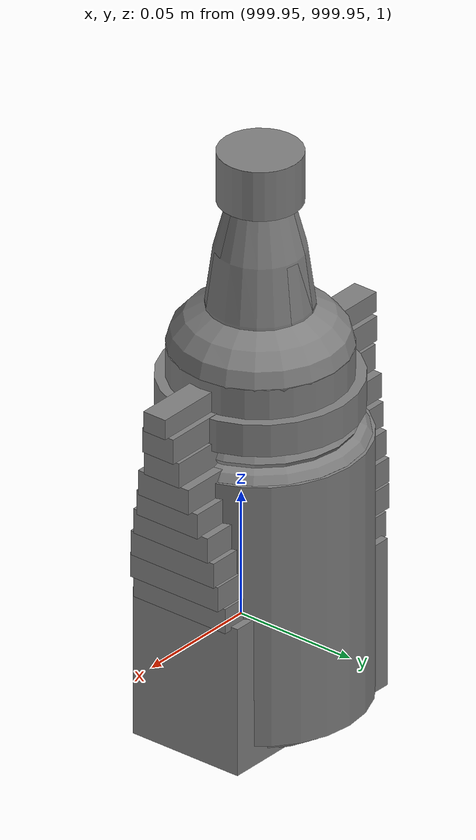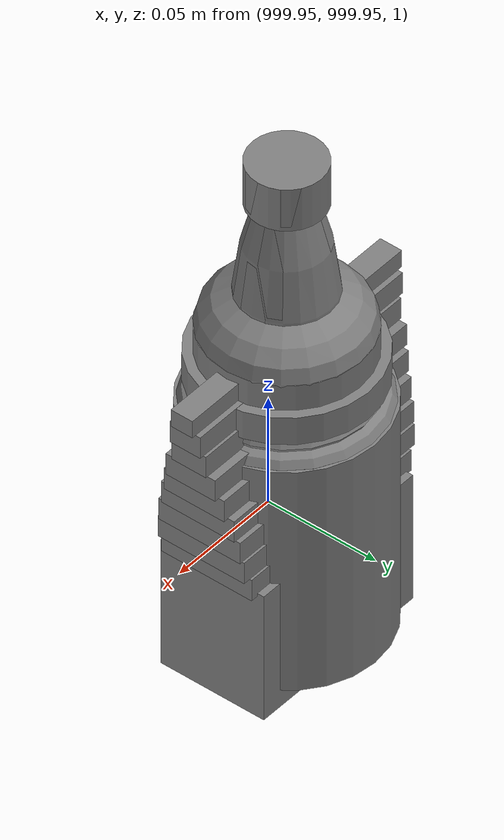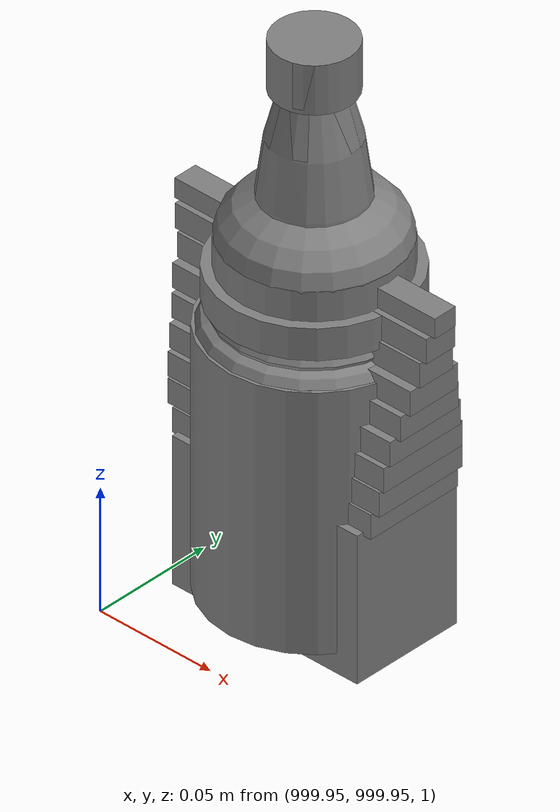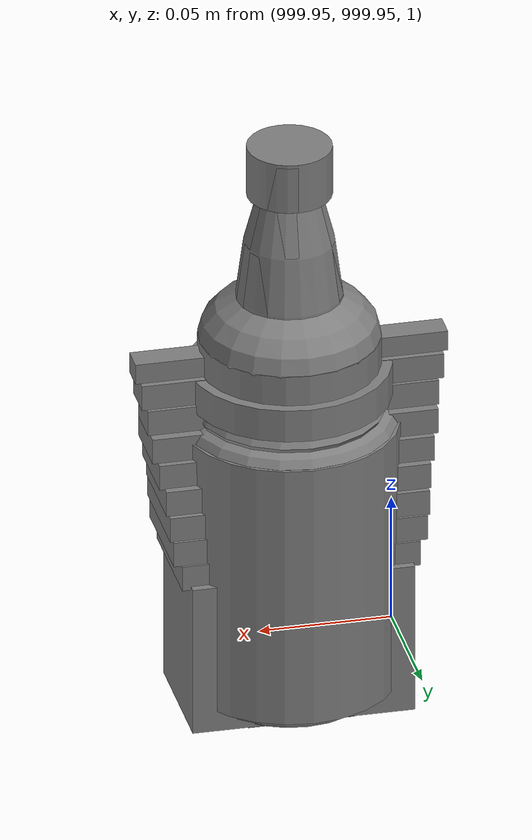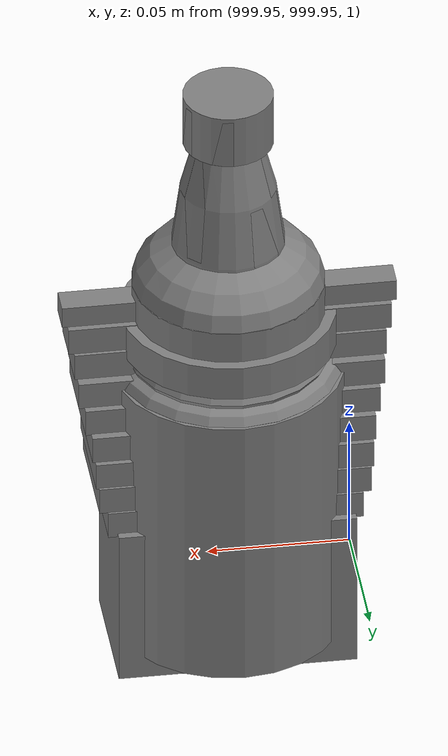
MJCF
<mujoco>
    <option gravity="0.000000000 0.000000000 -9.810000420" timestep="0.0166666" integrator="implicitfast" density="1.225" viscosity="1.8000001e-05" noslip_iterations="10" iterations="100" sdf_iterations="50">
        <flag multiccd="disable"/>
    </option>
    <size memory="1000M"/>
    <compiler coordinate="local"/>
    <worldbody>
        <light cutoff="30" pos="0 1 1" dir="0 -1 -2"/>
        <light cutoff="30" pos="0 -1 1" dir="0 1 -2"/>
        <body pos="-7.168000221 2.823999882 1.227496982" euler="-0.283413976 0.056829724 -0.133293271" name="openloong_gripper_2f85_fix_base_usda_Pos">
            <geom contype="1" conaffinity="1" density="1000" type="box" material="" rgba="0.500000000 0.500000000 0.500000000 1.000000000" solimp="0.899999976 0.949999988 0.001000000" friction="1.000000000 0.005000000 0.000100000" solref="0.020000000 1.000000000" margin="0" condim="3" group="0" pos="-0.002278805 0.074524641 -0.004134059" quat="0.315989345 0.948763072 -0.000000000 0.000000000" size="0.059999999 0.013000000 0.035000000" name="openloong_gripper_2f85_fix_base_usda_geom_3496ABF2_A6D2_4CBE_A585_586F8D39ED97"/>
            <geom contype="1" conaffinity="1" density="1000" type="box" material="" rgba="0.500000000 0.500000000 0.500000000 1.000000000" solimp="0.899999976 0.949999988 0.001000000" friction="1.000000000 0.005000000 0.000100000" solref="0.020000000 1.000000000" margin="0" condim="3" group="0" pos="-0.002278805 0.078031301 0.008128285" quat="0.990447521 -0.137893379 -0.000000000 -0.000000000" size="0.059999999 0.010000000 0.035000000" name="openloong_gripper_2f85_fix_base_usda_geom_9C5691D2_F7E8_413A_BABD_A8DA9B2EDD7B"/>
            <geom contype="1" conaffinity="1" density="1000" type="box" material="" rgba="0.500000000 0.500000000 0.500000000 1.000000000" solimp="0.899999976 0.949999988 0.001000000" friction="1.000000000 0.005000000 0.000100000" solref="0.020000000 1.000000000" margin="0" condim="3" group="0" pos="-0.002278805 0.080785275 -0.002596974" quat="0.287325472 -0.957833409 0.000000000 -0.000000000" size="0.059999999 0.013000000 0.035000000" name="openloong_gripper_2f85_fix_base_usda_geom_75A783EF_92F8_4BF5_A976_C751F6F89B6A"/>
            <geom contype="1" conaffinity="1" density="1000" type="box" material="" rgba="0.500000000 0.500000000 0.500000000 1.000000000" solimp="0.899999976 0.949999988 0.001000000" friction="1.000000000 0.005000000 0.000100000" solref="0.020000000 1.000000000" margin="0" condim="3" group="0" pos="-0.002278805 -0.098804474 -0.020146966" quat="0.988851666 0.148906454 0.000000000 -0.000000000" size="0.059999999 0.022000000 0.020000000" name="openloong_gripper_2f85_fix_base_usda_geom_CCDB6DD0_094F_43B8_8AB1_AD5CC448B306"/>
            <geom contype="1" conaffinity="1" density="1000" type="box" material="" rgba="0.500000000 0.500000000 0.500000000 1.000000000" solimp="0.899999976 0.949999988 0.001000000" friction="1.000000000 0.005000000 0.000100000" solref="0.020000000 1.000000000" margin="0" condim="3" group="0" pos="-0.002279282 0.019920111 0.012102962" quat="0.995421767 0.095583342 -0.000000000 -0.000000000" size="0.059999999 0.025000000 0.026000001" name="openloong_gripper_2f85_fix_base_usda_geom_5E842A7F_C4C2_46C8_B358_2D52DA66092C"/>
            <geom contype="1" conaffinity="1" density="1000" type="box" material="" rgba="0.500000000 0.500000000 0.500000000 1.000000000" solimp="0.899999976 0.949999988 0.001000000" friction="1.000000000 0.005000000 0.000100000" solref="0.020000000 1.000000000" margin="0" condim="3" group="0" pos="-0.002279282 0.005734444 -0.014276862" quat="0.999571741 -0.029275302 -0.000000000 -0.000000000" size="0.059999999 0.050000001 0.010000000" name="openloong_gripper_2f85_fix_base_usda_geom_DCA78A39_D0E1_49B5_9F3F_843B88F03829"/>
            <geom contype="1" conaffinity="1" density="1000" type="box" material="" rgba="0.500000000 0.500000000 0.500000000 1.000000000" solimp="0.899999976 0.949999988 0.001000000" friction="1.000000000 0.005000000 0.000100000" solref="0.020000000 1.000000000" margin="0" condim="3" group="0" pos="-0.002278805 0.079460382 0.007771969" quat="0.922590554 -0.385781586 0.000000000 -0.000000000" size="0.059999999 0.010000000 0.035000000" name="openloong_gripper_2f85_fix_base_usda_geom_4E2DCC71_C5AD_4484_94DB_FCBF97FA0BE2"/>
            <geom contype="1" conaffinity="1" density="1000" type="box" material="" rgba="0.500000000 0.500000000 0.500000000 1.000000000" solimp="0.899999976 0.949999988 0.001000000" friction="1.000000000 0.005000000 0.000100000" solref="0.020000000 1.000000000" margin="0" condim="3" group="0" pos="-0.002279282 0.081384182 -0.001320124" quat="0.590483785 -0.807049930 0.000000000 -0.000000000" size="0.059999999 0.013000000 0.035000000" name="openloong_gripper_2f85_fix_base_usda_geom_A1DDD785_64EA_4AA1_BAFF_FEBC3F542B57"/>
            <geom contype="1" conaffinity="1" density="1000" type="box" material="" rgba="0.500000000 0.500000000 0.500000000 1.000000000" solimp="0.899999976 0.949999988 0.001000000" friction="1.000000000 0.005000000 0.000100000" solref="0.020000000 1.000000000" margin="0" condim="3" group="0" pos="-0.002278805 -0.059297800 -0.007972836" quat="0.988851666 0.148906454 0.000000000 -0.000000000" size="0.059999999 0.020000000 0.022000000" name="openloong_gripper_2f85_fix_base_usda_geom_80BEACA0_EE96_48B9_A5CF_92EC9A4FB5BB"/>
            <geom contype="1" conaffinity="1" density="1000" type="box" material="" rgba="0.500000000 0.500000000 0.500000000 1.000000000" solimp="0.899999976 0.949999988 0.001000000" friction="1.000000000 0.005000000 0.000100000" solref="0.020000000 1.000000000" margin="0" condim="3" group="0" pos="-0.002278805 0.076618671 -0.004656792" quat="0.004634961 0.999989629 -0.000000000 0.000000000" size="0.059999999 0.013000000 0.035000000" name="openloong_gripper_2f85_fix_base_usda_geom_A03DD278_475B_44BB_85A9_9968D83BAF1A"/>
            <geom contype="1" conaffinity="1" density="1000" type="box" material="" rgba="0.500000000 0.500000000 0.500000000 1.000000000" solimp="0.899999976 0.949999988 0.001000000" friction="1.000000000 0.005000000 0.000100000" solref="0.020000000 1.000000000" margin="0" condim="3" group="0" pos="-0.002279282 -0.021952629 0.002960086" quat="0.991270423 0.131847665 -0.000000000 0.000000000" size="0.059999999 0.020000000 0.024000000" name="openloong_gripper_2f85_fix_base_usda_geom_91181D92_3512_4D7A_A464_C5FB58A10C9C"/>
            <geom contype="1" conaffinity="1" density="1000" type="box" material="" rgba="0.500000000 0.500000000 0.500000000 1.000000000" solimp="0.899999976 0.949999988 0.001000000" friction="1.000000000 0.005000000 0.000100000" solref="0.020000000 1.000000000" margin="0" condim="3" group="0" pos="-0.002278805 0.081418991 0.002587914" quat="0.803492308 -0.595315695 0.000000000 -0.000000000" size="0.059999999 0.013000000 0.035000000" name="openloong_gripper_2f85_fix_base_usda_geom_4B8C2F30_1C5D_4BD5_83B6_9DD1260FC51A"/>
            <geom contype="1" conaffinity="1" density="1000" type="box" material="" rgba="0.500000000 0.500000000 0.500000000 1.000000000" solimp="0.899999976 0.949999988 0.001000000" friction="1.000000000 0.005000000 0.000100000" solref="0.020000000 1.000000000" margin="0" condim="3" group="0" pos="-0.002278805 0.061115503 0.008545756" quat="0.999326169 0.036714450 0.000000000 -0.000000000" size="0.059999999 0.020000000 0.035000000" name="openloong_gripper_2f85_fix_base_usda_geom_41B9D3C3_6A0A_49FE_9360_B7BEE19FA1D5"/>
            <freejoint name="openloong_gripper_2f85_fix_base_usda_pos_scan"/>
        </body>
        <body pos="-3.510578632 3.403555870 -0.000000100" euler="0.000000000 0.000000000 40.200675964" name="openloong_gripper_2f85_fix_base_usda_PZ">
            <geom contype="1" conaffinity="1" density="1000" type="box" material="" rgba="0.500000000 0.500000000 0.500000000 1.000000000" solimp="0.899999976 0.949999988 0.001000000" friction="1.000000000 0.005000000 0.000100000" solref="0.020000000 1.000000000" margin="0" condim="3" group="0" pos="0.047452450 -0.054376602 0.374072611" quat="0.934387863 -0.082143910 -0.030358355 0.345326364" size="0.180000007 0.010000000 0.379999995" name="openloong_gripper_2f85_fix_base_usda_geom_A1EDA1B1_62A0_463C_B4E8_6D7ABF2FC070"/>
            <geom contype="1" conaffinity="1" density="1000" type="box" material="" rgba="0.500000000 0.500000000 0.500000000 1.000000000" solimp="0.899999976 0.949999988 0.001000000" friction="1.000000000 0.005000000 0.000100000" solref="0.020000000 1.000000000" margin="0" condim="3" group="0" pos="-0.047453165 0.056484699 0.373715430" quat="0.934750080 0.077914521 0.028795123 0.345459938" size="0.180000007 0.010000000 0.379999995" name="openloong_gripper_2f85_fix_base_usda_geom_1293C643_5DAF_49FE_8187_22B62AF7D74D"/>
            <freejoint name="openloong_gripper_2f85_fix_base_usda_PZ"/>
        </body>
        <body pos="-6.332345009 2.779978037 1.034067392" euler="0.000000000 0.000000000 0.000000000" name="openloong_gripper_2f85_fix_base_usda_basket">
            <geom contype="1" conaffinity="1" density="100000" type="box" material="" rgba="0.500000000 0.500000000 0.500000000 1.000000000" solimp="0.899999976 0.949999988 0.001000000" friction="1.000000000 0.899999976 0.000100000" solref="0.020000000 1.000000000" margin="0" condim="3" group="0" pos="-0.039724827 0.188377380 0.167089701" quat="0.997489929 -0.070808925 0.000000000 0.000000000" size="0.150000006 0.006000000 0.108000003" name="openloong_gripper_2f85_fix_base_usda_geom_DAF7DF73_03D8_4BF9_83D0_39114EB5CBC8"/>
            <geom contype="1" conaffinity="1" density="100000" type="box" material="" rgba="0.500000000 0.500000000 0.500000000 1.000000000" solimp="0.899999976 0.949999988 0.001000000" friction="1.000000000 0.899999976 0.000100000" solref="0.020000000 1.000000000" margin="0" condim="3" group="0" pos="-0.172339439 0.000000000 0.168361664" quat="0.706172407 -0.036353018 -0.036353093 0.706170976" size="0.200000003 0.006000000 0.108000003" name="openloong_gripper_2f85_fix_base_usda_geom_A89FB92C_E68A_4444_9CF6_F416B915112A"/>
            <geom contype="1" conaffinity="1" density="100000" type="box" material="" rgba="0.500000000 0.500000000 0.500000000 1.000000000" solimp="0.899999976 0.949999988 0.001000000" friction="1.000000000 0.899999976 0.000100000" solref="0.020000000 1.000000000" margin="0" condim="3" group="0" pos="-0.039724827 0.000000000 0.068126202" quat="1.000000000 0.000000000 0.000000000 0.000000000" size="0.129999995 0.174999997 0.006000000" name="openloong_gripper_2f85_fix_base_usda_geom_832B6204_9AFD_4FBB_A165_1A8D445B0B4A"/>
            <geom contype="1" conaffinity="1" density="100000" type="box" material="" rgba="0.500000000 0.500000000 0.500000000 1.000000000" solimp="0.899999976 0.949999988 0.001000000" friction="1.000000000 0.899999976 0.000100000" solref="0.020000000 1.000000000" margin="0" condim="3" group="0" pos="-0.039724827 -0.188568115 0.167089701" quat="0.997537494 0.070135131 0.000000000 0.000000000" size="0.150000006 0.006000000 0.108000003" name="openloong_gripper_2f85_fix_base_usda_geom_909D84A3_62FC_490B_B133_7A2EF1FB3155"/>
            <geom contype="1" conaffinity="1" density="100000" type="box" material="" rgba="0.500000000 0.500000000 0.500000000 1.000000000" solimp="0.899999976 0.949999988 0.001000000" friction="1.000000000 0.899999976 0.000100000" solref="0.020000000 1.000000000" margin="0" condim="3" group="0" pos="0.094372749 0.000000000 0.168361664" quat="0.706172049 0.036353335 0.036353379 0.706171215" size="0.200000003 0.006000000 0.108000003" name="openloong_gripper_2f85_fix_base_usda_geom_08701A4D_2D9C_452E_BAA2_A4EEE95889D4"/>
            <freejoint name="openloong_gripper_2f85_fix_base_usda_basket_joint"/>
            <site size="0.005000000 0.005000000 0.005000000" rgba="0.500000000 0.500000000 0.500000000 1.000000000" pos="0.000000000 0.000000000 0.000000000" quat="1.000000000 0.000000000 0.000000000 0.000000000" group="0" type="sphere" name="openloong_gripper_2f85_fix_base_usda_basketsite"/>
        </body>
        <body pos="0.000000000 0.000000000 0.000000000" euler="0.000000000 0.000000000 0.000000000" name="Interactive Objects_Interactive Objects"/>
        <body pos="0.000000000 0.000000000 0.000000000" euler="0.000000000 0.000000000 0.000000000" name=" Static Objects_ Static Objects">
            <geom contype="1" conaffinity="1" density="1000" type="box" material="" rgba="0.500000000 0.500000000 0.500000000 1.000000000" solimp="0.899999976 0.949999988 0.001000000" friction="1.000000000 0.005000000 0.000100000" solref="0.020000000 1.000000000" margin="0" condim="3" group="0" pos="-12.050000191 10.000000000 2.000000000" quat="1.000000000 0.000000000 0.000000000 0.000000000" size="0.070000000 10.500000000 2.000000000" name=" Static Objects_geom_234B7988_4091_4138_B87D_7659211DFB57"/>
            <geom contype="1" conaffinity="1" density="1000" type="box" material="" rgba="0.500000000 0.500000000 0.500000000 1.000000000" solimp="0.899999976 0.949999988 0.001000000" friction="1.000000000 0.005000000 0.000100000" solref="0.020000000 1.000000000" margin="0" condim="3" group="0" pos="0.000000000 10.000000000 2.000000000" quat="1.000000000 0.000000000 0.000000000 0.000000000" size="0.070000000 10.500000000 2.000000000" name=" Static Objects_geom_02939BDF_C408_4F8B_99CB_60923AFD95DF"/>
            <geom contype="1" conaffinity="1" density="1000" type="box" material="" rgba="0.500000000 0.500000000 0.500000000 1.000000000" solimp="0.899999976 0.949999988 0.001000000" friction="1.000000000 0.005000000 0.000100000" solref="0.020000000 1.000000000" margin="0" condim="3" group="0" pos="-6.000000000 20.159999847 2.000000000" quat="1.000000000 0.000000000 0.000000000 0.000000000" size="6.079999924 0.070000000 2.000000000" name=" Static Objects_geom_8594ED92_8A37_499D_A2D2_502970D9B78C"/>
            <geom contype="1" conaffinity="1" density="1000" type="box" material="" rgba="0.500000000 0.500000000 0.500000000 1.000000000" solimp="0.899999976 0.949999988 0.001000000" friction="1.000000000 0.005000000 0.000100000" solref="0.020000000 1.000000000" margin="0" condim="3" group="0" pos="-6.000000000 0.035000000 2.000000000" quat="1.000000000 0.000000000 0.000000000 0.000000000" size="6.079999924 0.070000000 2.000000000" name=" Static Objects_geom_33B09484_22C7_4923_95E3_23FDD55F8ACF"/>
            <geom contype="1" conaffinity="1" density="1000" type="plane" material="" rgba="0.500000000 0.500000000 0.500000000 1.000000000" solimp="0.899999976 0.949999988 0.001000000" friction="1.000000000 0.005000000 0.000100000" solref="0.020000000 1.000000000" margin="0" condim="3" group="0" pos="-6.000000000 10.399999619 0.000000000" quat="1.000000000 0.000000000 0.000000000 0.000000000" size="6.050000191 10.800000191 0.010000000" name=" Static Objects_geom_0549946C_A6A9_4381_8B6C_326B498FB3A3"/>
            <geom contype="1" conaffinity="1" density="1000" type="box" material="" rgba="0.500000000 0.500000000 0.500000000 1.000000000" solimp="0.899999976 0.949999988 0.001000000" friction="1.000000000 0.005000000 0.000100000" solref="0.020000000 1.000000000" margin="0" condim="3" group="0" pos="-6.098561764 6.327973843 1.292199373" quat="1.000000000 0.000000000 0.000000000 0.000000000" size="0.500000000 0.100000001 0.150000006" name=" Static Objects_geom_FC27E0DB_DA60_4CB1_AB95_9A219C16516A"/>
            <geom contype="1" conaffinity="1" density="1000" type="box" material="" rgba="0.500000000 0.500000000 0.500000000 1.000000000" solimp="0.899999976 0.949999988 0.001000000" friction="1.000000000 0.005000000 0.000100000" solref="0.020000000 1.000000000" margin="0" condim="3" group="0" pos="-8.844120979 6.464855671 1.209077358" quat="1.000000000 0.000000000 0.000000000 0.000000000" size="0.100000001 0.100000001 0.070000000" name=" Static Objects_geom_D499E36B_3CFF_484D_BCCD_D01D7664C7F1"/>
            <geom contype="1" conaffinity="1" density="1000" type="box" material="" rgba="0.500000000 0.500000000 0.500000000 1.000000000" solimp="0.899999976 0.949999988 0.001000000" friction="1.000000000 0.005000000 0.000100000" solref="0.020000000 1.000000000" margin="0" condim="3" group="0" pos="-7.373087406 6.458900928 1.214329123" quat="1.000000000 0.000000000 0.000000000 0.000000000" size="0.250000000 0.200000003 0.075000003" name=" Static Objects_geom_EDACFAFD_5A48_4526_A92F_02D222EAB361"/>
            <geom contype="1" conaffinity="1" density="1000" type="box" material="" rgba="0.500000000 0.500000000 0.500000000 1.000000000" solimp="0.899999976 0.949999988 0.001000000" friction="1.000000000 0.005000000 0.000100000" solref="0.020000000 1.000000000" margin="0" condim="3" group="0" pos="-5.611940861 6.318420410 0.350975692" quat="1.000000000 0.000000000 0.000000000 0.000000000" size="0.699999988 0.100000001 0.150000006" name=" Static Objects_geom_EF20EC53_1B2D_4D3E_B955_1F7BC0039AF9"/>
            <geom contype="1" conaffinity="1" density="1000" type="box" material="" rgba="0.500000000 0.500000000 0.500000000 1.000000000" solimp="0.899999976 0.949999988 0.001000000" friction="1.000000000 0.005000000 0.000100000" solref="0.020000000 1.000000000" margin="0" condim="3" group="0" pos="-6.924745083 6.362090111 1.214329123" quat="1.000000000 0.000000000 0.000000000 0.000000000" size="0.200000003 0.100000001 0.075000003" name=" Static Objects_geom_B10E7571_551A_4112_B381_B989113A03D8"/>
            <geom contype="1" conaffinity="1" density="1000" type="box" material="" rgba="0.500000000 0.500000000 0.500000000 1.000000000" solimp="0.899999976 0.949999988 0.001000000" friction="1.000000000 0.005000000 0.000100000" solref="0.020000000 1.000000000" margin="0" condim="3" group="0" pos="-9.237723351 6.464855671 1.209077358" quat="1.000000000 0.000000000 0.000000000 0.000000000" size="0.100000001 0.100000001 0.070000000" name=" Static Objects_geom_C0474B28_32F1_48BD_8F54_818DA21D08FC"/>
            <geom contype="1" conaffinity="1" density="1000" type="box" material="" rgba="0.500000000 0.500000000 0.500000000 1.000000000" solimp="0.899999976 0.949999988 0.001000000" friction="1.000000000 0.005000000 0.000100000" solref="0.020000000 1.000000000" margin="0" condim="3" group="0" pos="-6.824534416 6.447464466 1.212718010" quat="1.000000000 0.000000000 0.000000000 0.000000000" size="0.100000001 0.100000001 0.075000003" name=" Static Objects_geom_64746021_92D9_4E97_9209_7354EFD44FC6"/>
            <geom contype="1" conaffinity="1" density="1000" type="box" material="" rgba="0.500000000 0.500000000 0.500000000 1.000000000" solimp="0.899999976 0.949999988 0.001000000" friction="1.000000000 0.005000000 0.000100000" solref="0.020000000 1.000000000" margin="0" condim="3" group="0" pos="-6.751636982 6.459744930 0.800981164" quat="1.000000000 0.000000000 0.000000000 0.000000000" size="2.200000048 0.200000003 0.150000006" name=" Static Objects_geom_D4CB6511_2397_4052_AA09_5DC70CA5FA19"/>
            <geom contype="1" conaffinity="1" density="1000" type="box" material="" rgba="0.500000000 0.500000000 0.500000000 1.000000000" solimp="0.899999976 0.949999988 0.001000000" friction="1.000000000 0.005000000 0.000100000" solref="0.020000000 1.000000000" margin="0" condim="3" group="0" pos="-3.907610416 6.318625927 0.800981164" quat="1.000000000 0.000000000 0.000000000 0.000000000" size="0.500000000 0.100000001 0.150000006" name=" Static Objects_geom_8AABFDBE_BD29_4CA5_8B7E_396DB08B0A73"/>
            <geom contype="1" conaffinity="1" density="1000" type="box" material="" rgba="0.500000000 0.500000000 0.500000000 1.000000000" solimp="0.899999976 0.949999988 0.001000000" friction="1.000000000 0.005000000 0.000100000" solref="0.020000000 1.000000000" margin="0" condim="3" group="0" pos="-7.886891365 6.459744930 0.352518857" quat="1.000000000 0.000000000 0.000000000 0.000000000" size="1.500000000 0.200000003 0.150000006" name=" Static Objects_geom_2B935D2F_9D73_4E8F_B263_2F9A688E1CAC"/>
            <geom contype="1" conaffinity="1" density="1000" type="box" material="" rgba="0.500000000 0.500000000 0.500000000 1.000000000" solimp="0.899999976 0.949999988 0.001000000" friction="1.000000000 0.005000000 0.000100000" solref="0.020000000 1.000000000" margin="0" condim="3" group="0" pos="-4.407354832 6.459744930 1.292199373" quat="1.000000000 0.000000000 0.000000000 0.000000000" size="1.240000010 0.200000003 0.150000006" name=" Static Objects_geom_D80C8669_1B6B_4750_BF76_4B6E1384ACC5"/>
            <geom contype="1" conaffinity="1" density="1000" type="box" material="" rgba="0.500000000 0.500000000 0.500000000 1.000000000" solimp="0.899999976 0.949999988 0.001000000" friction="1.000000000 0.005000000 0.000100000" solref="0.020000000 1.000000000" margin="0" condim="3" group="0" pos="-9.058088303 6.434794426 1.209077358" quat="1.000000000 0.000000000 0.000000000 0.000000000" size="0.250000000 0.100000001 0.070000000" name=" Static Objects_geom_6BD033A7_2AE4_402B_9AEE_EF360B90A78F"/>
            <geom contype="1" conaffinity="1" density="1000" type="box" material="" rgba="0.500000000 0.500000000 0.500000000 1.000000000" solimp="0.899999976 0.949999988 0.001000000" friction="1.000000000 0.005000000 0.000100000" solref="0.020000000 1.000000000" margin="0" condim="3" group="0" pos="-6.300771236 6.459744930 1.744376063" quat="1.000000000 0.000000000 0.000000000 0.000000000" size="3.000000000 0.200000003 0.150000006" name=" Static Objects_geom_44EA5F28_4E41_48DB_9F32_4E79B4E13D13"/>
            <geom contype="1" conaffinity="1" density="1000" type="box" material="" rgba="0.500000000 0.500000000 0.500000000 1.000000000" solimp="0.899999976 0.949999988 0.001000000" friction="1.000000000 0.005000000 0.000100000" solref="0.020000000 1.000000000" margin="0" condim="3" group="0" pos="-4.035642624 6.459744930 0.352518857" quat="1.000000000 0.000000000 0.000000000 0.000000000" size="0.800000012 0.200000003 0.150000006" name=" Static Objects_geom_302AB6C6_60CD_40B1_A25F_4CD45E7A6C51"/>
            <geom contype="1" conaffinity="1" density="1000" type="box" material="" rgba="0.500000000 0.500000000 0.500000000 1.000000000" solimp="0.899999976 0.949999988 0.001000000" friction="1.000000000 0.005000000 0.000100000" solref="0.020000000 1.000000000" margin="0" condim="3" group="0" pos="-6.286010742 6.153595448 0.629031777" quat="0.707107067 0.000000000 0.000000000 0.707106471" size="0.529999971 3.134999990 0.025000000" name=" Static Objects_geom_7EAE16C7_0EDE_4197_B815_C8613B192B26"/>
            <geom contype="1" conaffinity="1" density="1000" type="box" material="" rgba="0.500000000 0.500000000 0.500000000 1.000000000" solimp="0.899999976 0.949999988 0.001000000" friction="1.000000000 0.005000000 0.000100000" solref="0.020000000 1.000000000" margin="0" condim="3" group="0" pos="-2.825197220 6.153595448 1.113528371" quat="0.707107067 0.000000000 0.000000000 0.707106471" size="0.550000012 0.239999995 0.025000000" name=" Static Objects_geom_5A87A9CA_4455_468B_8435_9A8C5D6EC511"/>
            <geom contype="1" conaffinity="1" density="1000" type="box" material="" rgba="0.500000000 0.500000000 0.500000000 1.000000000" solimp="0.899999976 0.949999988 0.001000000" friction="1.000000000 0.005000000 0.000100000" solref="0.020000000 1.000000000" margin="0" condim="3" group="0" pos="-2.825197220 6.153595448 0.629031777" quat="0.707107067 0.000000000 0.000000000 0.707106471" size="0.550000012 0.239999995 0.025000000" name=" Static Objects_geom_51B4039F_2315_4749_AE8B_DED3175A83CA"/>
            <geom contype="1" conaffinity="1" density="1000" type="box" material="" rgba="0.500000000 0.500000000 0.500000000 1.000000000" solimp="0.899999976 0.949999988 0.001000000" friction="1.000000000 0.005000000 0.000100000" solref="0.020000000 1.000000000" margin="0" condim="3" group="0" pos="-2.825197220 6.153595448 1.563861728" quat="0.707107067 0.000000000 0.000000000 0.707106471" size="0.550000012 0.239999995 0.025000000" name=" Static Objects_geom_813CD900_D373_4A5B_8A9C_F2FFBCD9C868"/>
            <geom contype="1" conaffinity="1" density="1000" type="box" material="" rgba="0.500000000 0.500000000 0.500000000 1.000000000" solimp="0.899999976 0.949999988 0.001000000" friction="1.000000000 0.005000000 0.000100000" solref="0.020000000 1.000000000" margin="0" condim="3" group="0" pos="-6.311686516 6.153595448 1.018643856" quat="0.707107067 0.000000000 0.000000000 0.707106471" size="0.050000001 3.150000095 1.019999981" name=" Static Objects_geom_A6592FD3_A1B1_4D98_AE2A_409CEDE3D204"/>
            <geom contype="1" conaffinity="1" density="1000" type="box" material="" rgba="0.500000000 0.500000000 0.500000000 1.000000000" solimp="0.899999976 0.949999988 0.001000000" friction="1.000000000 0.005000000 0.000100000" solref="0.020000000 1.000000000" margin="0" condim="3" group="0" pos="-3.101639986 6.150595188 1.018643856" quat="1.000000000 0.000000000 0.000000000 0.000000000" size="0.050000001 0.579999983 1.019999981" name=" Static Objects_geom_7BBBF075_B6EE_4B05_AB4D_C5B33E5C709D"/>
            <geom contype="1" conaffinity="1" density="1000" type="box" material="" rgba="0.500000000 0.500000000 0.500000000 1.000000000" solimp="0.899999976 0.949999988 0.001000000" friction="1.000000000 0.005000000 0.000100000" solref="0.020000000 1.000000000" margin="0" condim="3" group="0" pos="-2.825197220 6.153595448 0.097434282" quat="0.707107067 0.000000000 0.000000000 0.707106471" size="0.550000012 0.239999995 0.098999999" name=" Static Objects_geom_161F575B_807C_4FD3_B64D_87E3EA9CF3E1"/>
            <geom contype="1" conaffinity="1" density="1000" type="box" material="" rgba="0.500000000 0.500000000 0.500000000 1.000000000" solimp="0.899999976 0.949999988 0.001000000" friction="1.000000000 0.005000000 0.000100000" solref="0.020000000 1.000000000" margin="0" condim="3" group="0" pos="-6.286010742 6.153595448 0.096129179" quat="0.707107067 0.000000000 0.000000000 0.707106471" size="0.529999971 3.134999990 0.098999999" name=" Static Objects_geom_2E2D5285_790F_45E1_8E1F_865229BFF721"/>
            <geom contype="1" conaffinity="1" density="1000" type="box" material="" rgba="0.500000000 0.500000000 0.500000000 1.000000000" solimp="0.899999976 0.949999988 0.001000000" friction="1.000000000 0.005000000 0.000100000" solref="0.020000000 1.000000000" margin="0" condim="3" group="0" pos="-6.286010742 6.153595448 1.563861728" quat="0.707107067 0.000000000 0.000000000 0.707106471" size="0.529999971 3.134999990 0.025000000" name=" Static Objects_geom_0A576ADC_5409_43AE_8FC3_14A21E23F937"/>
            <geom contype="1" conaffinity="1" density="1000" type="box" material="" rgba="0.500000000 0.500000000 0.500000000 1.000000000" solimp="0.899999976 0.949999988 0.001000000" friction="1.000000000 0.005000000 0.000100000" solref="0.020000000 1.000000000" margin="0" condim="3" group="0" pos="-6.293097973 6.153595448 1.114443064" quat="0.707107067 0.000000000 0.000000000 0.707106471" size="0.529999971 3.134999990 0.025000000" name=" Static Objects_geom_B220B502_EE28_45DA_8D7F_AC0F51B13C36"/>
            <geom contype="1" conaffinity="1" density="1000" type="box" material="" rgba="0.500000000 0.500000000 0.500000000 1.000000000" solimp="0.899999976 0.949999988 0.001000000" friction="1.000000000 0.005000000 0.000100000" solref="0.020000000 1.000000000" margin="0" condim="3" group="0" pos="-7.437745571 3.067511320 1.289965630" quat="1.000000000 0.000000000 0.000000000 0.000000000" size="0.029999999 0.020000000 0.020000000" name=" Static Objects_geom_389B4F26_4A4A_4BDC_AC5B_AB1583AF3D9B"/>
            <geom contype="1" conaffinity="1" density="1000" type="box" material="" rgba="0.500000000 0.500000000 0.500000000 1.000000000" solimp="0.899999976 0.949999988 0.001000000" friction="1.000000000 0.005000000 0.000100000" solref="0.020000000 1.000000000" margin="0" condim="3" group="0" pos="-7.719123363 2.958004713 1.530241251" quat="1.000000000 0.000000000 0.000000000 0.000000000" size="0.250000000 0.159999996 0.280000001" name=" Static Objects_geom_F2858744_2D04_44CC_AF0D_1B3E3DE7970B"/>
            <geom contype="1" conaffinity="1" density="1000" type="box" material="" rgba="0.500000000 0.500000000 0.500000000 1.000000000" solimp="0.899999976 0.949999988 0.001000000" friction="1.000000000 0.005000000 0.000100000" solref="0.020000000 1.000000000" margin="0" condim="3" group="0" pos="-7.719123363 2.867671013 1.173410416" quat="1.000000000 0.000000000 0.000000000 0.000000000" size="0.250000000 0.250000000 0.079999998" name=" Static Objects_geom_8324811D_5601_4BEC_9487_1C602F3EC91B"/>
            <geom contype="1" conaffinity="1" density="1000" type="cylinder" material="" rgba="0.500000000 0.500000000 0.500000000 1.000000000" solimp="0.899999976 0.949999988 0.001000000" friction="1.000000000 0.005000000 0.000100000" solref="0.020000000 1.000000000" margin="0" condim="3" group="0" pos="-7.427312374 3.069516420 1.502544641" quat="0.928051054 0.000000000 0.000000000 0.372453064" size="0.015000000 0.230000004 0.100000001" name=" Static Objects_geom_3879FD80_0319_4F5C_A001_72B31A552EBC"/>
            <geom contype="1" conaffinity="1" density="1000" type="box" material="" rgba="0.500000000 0.500000000 0.500000000 1.000000000" solimp="0.899999976 0.949999988 0.001000000" friction="1.000000000 0.005000000 0.000100000" solref="0.020000000 1.000000000" margin="0" condim="3" group="0" pos="-7.408766270 3.088089943 1.776644945" quat="0.928051054 0.000000000 0.000000000 0.372453064" size="0.050000001 0.100000001 0.050000001" name=" Static Objects_geom_1442327F_6E4E_4F25_9798_B8A6EF465D68"/>
            <geom contype="1" conaffinity="1" density="1000" type="box" material="" rgba="0.500000000 0.500000000 0.500000000 1.000000000" solimp="0.899999976 0.949999988 0.001000000" friction="1.000000000 0.005000000 0.000100000" solref="0.020000000 1.000000000" margin="0" condim="3" group="0" pos="-4.240264893 1.327049494 0.549888909" quat="1.000000000 0.000000000 0.000000000 0.000000000" size="0.430000007 1.200000048 0.550000012" name=" Static Objects_geom_85180F20_05D8_430C_88E4_80309DF929BF"/>
            <geom contype="1" conaffinity="1" density="1000" type="box" material="" rgba="0.500000000 0.500000000 0.500000000 1.000000000" solimp="0.899999976 0.949999988 0.001000000" friction="1.000000000 0.005000000 0.000100000" solref="0.020000000 1.000000000" margin="0" condim="3" group="0" pos="-6.460197449 2.937205315 0.548931718" quat="1.000000000 0.000000000 0.000000000 0.000000000" size="2.650000095 0.430000007 0.550000012" name=" Static Objects_geom_BAF11516_C4D6_4DCB_B9DD_E72028F70F2B"/>
            <geom contype="1" conaffinity="1" density="1000" type="box" material="" rgba="0.500000000 0.500000000 0.500000000 1.000000000" solimp="0.899999976 0.949999988 0.001000000" friction="1.000000000 0.005000000 0.000100000" solref="0.020000000 1.000000000" margin="0" condim="3" group="0" pos="-8.830721855 2.096410990 0.549305558" quat="1.000000000 0.000000000 0.000000000 0.000000000" size="0.280000001 0.430000007 0.550000012" name=" Static Objects_geom_F651E141_ACB5_45F3_8F58_19EF7255F59D"/>
        </body>
        <body pos="1000.000000000 1000.000000000 1.000000000" euler="0.000000000 0.000000000 0.000000000" name="openloong_gripper_2f85_fix_base_usda_bottle_blue">
            <geom contype="1" conaffinity="1" density="1000" type="ellipsoid" material="" rgba="0.500000000 0.500000000 0.500000000 1.000000000" solimp="0.899999976 0.949999988 0.001000000" friction="1.000000000 0.005000000 0.000100000" solref="0.020000000 1.000000000" margin="0" condim="3" group="0" pos="0.000000000 0.000000000 0.118920922" quat="1.000000000 0.000000000 0.000000000 0.000000000" size="0.030999999 0.030999999 0.029999999" name="openloong_gripper_2f85_fix_base_usda_geom_0C4AD130_8902_4103_823F_47C959927CAE"/>
            <geom contype="1" conaffinity="1" density="1000" type="box" material="" rgba="0.500000000 0.500000000 0.500000000 1.000000000" solimp="0.899999976 0.949999988 0.001000000" friction="1.000000000 0.005000000 0.000100000" solref="0.020000000 1.000000000" margin="0" condim="3" group="0" pos="0.000000000 0.000000000 0.002164602" quat="1.000000000 0.000000000 0.000000000 0.000000000" size="0.020000000 0.020000000 0.003000000" name="openloong_gripper_2f85_fix_base_usda_geom_493B1291_FFBF_4E97_91A4_0832A07E60E5"/>
            <geom contype="1" conaffinity="1" density="1000" type="cylinder" material="" rgba="0.500000000 0.500000000 0.500000000 1.000000000" solimp="0.899999976 0.949999988 0.001000000" friction="1.000000000 0.005000000 0.000100000" solref="0.020000000 1.000000000" margin="0" condim="3" group="0" pos="0.000000000 -0.000366211 0.060859680" quat="1.000000000 0.000000000 0.000000000 0.000000000" size="0.030999999 0.057999998 1.000000000" name="openloong_gripper_2f85_fix_base_usda_geom_AF189FA2_9124_444E_84FF_249C6F21A8CC"/>
            <geom contype="1" conaffinity="1" density="1000" type="cylinder" material="" rgba="0.500000000 0.500000000 0.500000000 1.000000000" solimp="0.899999976 0.949999988 0.001000000" friction="1.000000000 0.005000000 0.000100000" solref="0.020000000 1.000000000" margin="0" condim="3" group="0" pos="0.000000000 0.000000000 0.220594406" quat="1.000000000 0.000000000 0.000000000 0.000000000" size="0.016000001 0.010000000 1.000000000" name="openloong_gripper_2f85_fix_base_usda_geom_AA7E291C_F636_4A65_A2E0_EC2FE4EAD1D5"/>
            <geom contype="1" conaffinity="1" density="1000" type="ellipsoid" material="" rgba="0.500000000 0.500000000 0.500000000 1.000000000" solimp="0.899999976 0.949999988 0.001000000" friction="1.000000000 0.005000000 0.000100000" solref="0.020000000 1.000000000" margin="0" condim="3" group="0" pos="0.000000000 0.000000000 0.144259930" quat="1.000000000 0.000000000 0.000000000 0.000000000" size="0.021000000 0.021000000 0.079999998" name="openloong_gripper_2f85_fix_base_usda_geom_40B2B225_42D8_4E55_802C_F5D6F7008CD1"/>
            <freejoint name="openloong_gripper_2f85_fix_base_usda_bottle_blue_joint"/>
            <site size="0.005000000 0.005000000 0.005000000" rgba="0.500000000 0.500000000 0.500000000 1.000000000" pos="0.000000000 0.000000000 0.000000000" quat="0.999961913 0.008726535 0.000000000 0.000000000" group="0" type="sphere" name="openloong_gripper_2f85_fix_base_usda_bottle_bluesite"/>
        </body>
        <body pos="-5.901105881 2.237576962 2.332792997" euler="164.779434204 -40.129467010 -58.036304474" mocap="true" name="spotlight6_SpotLight"/>
        <body pos="-6.314171314 2.388265848 2.502977133" euler="-162.540008545 5.643122196 -26.637760162" mocap="true" name="spotlight4_SpotLight"/>
        <body pos="1000.000000000 1000.000000000 1.000000000" euler="0.000000000 0.000000000 0.000000000" name="openloong_gripper_2f85_fix_base_usda_can">
            <geom contype="1" conaffinity="1" density="1000" type="cylinder" material="" rgba="0.500000000 0.500000000 0.500000000 1.000000000" solimp="0.899999976 0.949999988 0.001000000" friction="1.000000000 0.005000000 0.000100000" solref="0.020000000 1.000000000" margin="0" condim="3" group="0" pos="0.000000000 0.000000000 0.079676986" quat="1.000000000 0.000000000 0.000000000 0.000000000" size="0.034000002 0.071999997 1.000000000" name="openloong_gripper_2f85_fix_base_usda_geom_331C41F5_E8E6_4D4C_BC89_C4A49AAA8670"/>
            <geom contype="1" conaffinity="1" density="1000" type="ellipsoid" material="" rgba="0.500000000 0.500000000 0.500000000 1.000000000" solimp="0.899999976 0.949999988 0.001000000" friction="1.000000000 0.005000000 0.000100000" solref="0.020000000 1.000000000" margin="0" condim="3" group="0" pos="0.000000000 0.000000000 0.151854277" quat="1.000000000 0.000000000 0.000000000 0.000000000" size="0.034000002 0.034000002 0.020000000" name="openloong_gripper_2f85_fix_base_usda_geom_EF301E90_AAE5_46F3_B97B_378E2123DC71"/>
            <geom contype="1" conaffinity="1" density="1000" type="box" material="" rgba="0.500000000 0.500000000 0.500000000 1.000000000" solimp="0.899999976 0.949999988 0.001000000" friction="1.000000000 0.005000000 0.000100000" solref="0.020000000 1.000000000" margin="0" condim="3" group="0" pos="0.000000000 0.000000000 0.004777670" quat="1.000000000 0.000000000 0.000000000 0.000000000" size="0.020000000 0.020000000 0.005000000" name="openloong_gripper_2f85_fix_base_usda_geom_71813F42_E70A_4245_8AE1_BC1DE99D4D77"/>
            <freejoint name="openloong_gripper_2f85_fix_base_usda_can_joint"/>
            <site size="0.005000000 0.005000000 0.005000000" rgba="0.500000000 0.500000000 0.500000000 1.000000000" pos="0.000000000 0.000000000 0.000000000" quat="1.000000000 0.000000000 0.000000000 0.000000000" group="0" type="sphere" name="openloong_gripper_2f85_fix_base_usda_cansite"/>
        </body>
        <body pos="-6.001734734 2.070628166 2.391187429" euler="-109.005615234 72.103073120 -5.888400555" mocap="true" name="spotlight3_SpotLight"/>
        <body pos="1000.000000000 1000.000000000 1.000000000" euler="0.000000000 0.000000000 0.000000000" name="openloong_gripper_2f85_fix_base_usda_jar_01">
            <geom contype="1" conaffinity="1" density="1000" type="box" material="" rgba="0.500000000 0.500000000 0.500000000 1.000000000" solimp="0.899999976 0.949999988 0.001000000" friction="1.000000000 0.005000000 0.000100000" solref="0.020000000 1.000000000" margin="0" condim="3" group="0" pos="0.000000000 0.000000000 0.006158113" quat="1.000000000 0.000000000 0.000000000 0.000000000" size="0.020000000 0.020000000 0.005000000" name="openloong_gripper_2f85_fix_base_usda_geom_8DE37993_8570_405E_B69D_871D59BA131C"/>
            <geom contype="1" conaffinity="1" density="1000" type="cylinder" material="" rgba="0.500000000 0.500000000 0.500000000 1.000000000" solimp="0.899999976 0.949999988 0.001000000" friction="1.000000000 0.005000000 0.000100000" solref="0.020000000 1.000000000" margin="0" condim="3" group="0" pos="0.000000000 0.000000000 0.062744498" quat="1.000000000 0.000000000 0.000000000 0.000000000" size="0.041000001 0.052999999 1.000000000" name="openloong_gripper_2f85_fix_base_usda_geom_7EF2788E_5FBE_4C7D_9D83_1AE7ACC9CAED"/>
            <geom contype="1" conaffinity="1" density="1000" type="ellipsoid" material="" rgba="0.500000000 0.500000000 0.500000000 1.000000000" solimp="0.899999976 0.949999988 0.001000000" friction="1.000000000 0.005000000 0.000100000" solref="0.020000000 1.000000000" margin="0" condim="3" group="0" pos="0.000000000 0.000000000 0.122252703" quat="1.000000000 0.000000000 0.000000000 0.000000000" size="0.035999998 0.035999998 0.010000000" name="openloong_gripper_2f85_fix_base_usda_geom_31E77554_9F9F_40FE_8436_E650A1F6E7E3"/>
            <geom contype="1" conaffinity="1" density="1000" type="cylinder" material="" rgba="0.500000000 0.500000000 0.500000000 1.000000000" solimp="0.899999976 0.949999988 0.001000000" friction="1.000000000 0.005000000 0.000100000" solref="0.020000000 1.000000000" margin="0" condim="3" group="0" pos="0.000000000 0.000000000 0.015747190" quat="1.000000000 0.000000000 0.000000000 0.000000000" size="0.035000000 0.010000000 1.000000000" name="openloong_gripper_2f85_fix_base_usda_geom_A6186E68_94E7_461A_B303_7CA9A5EDB27D"/>
            <geom contype="1" conaffinity="1" density="1000" type="ellipsoid" material="" rgba="0.500000000 0.500000000 0.500000000 1.000000000" solimp="0.899999976 0.949999988 0.001000000" friction="1.000000000 0.005000000 0.000100000" solref="0.020000000 1.000000000" margin="0" condim="3" group="0" pos="0.000000000 0.000000000 0.115815401" quat="1.000000000 0.000000000 0.000000000 0.000000000" size="0.039999999 0.039999999 0.010000000" name="openloong_gripper_2f85_fix_base_usda_geom_C9426E19_2ACE_4E7D_A116_9A7E708E024A"/>
            <geom contype="1" conaffinity="1" density="1000" type="cylinder" material="" rgba="0.500000000 0.500000000 0.500000000 1.000000000" solimp="0.899999976 0.949999988 0.001000000" friction="1.000000000 0.005000000 0.000100000" solref="0.020000000 1.000000000" margin="0" condim="3" group="0" pos="0.000000000 0.000000000 0.133183479" quat="1.000000000 0.000000000 0.000000000 0.000000000" size="0.037999999 0.006500000 1.000000000" name="openloong_gripper_2f85_fix_base_usda_geom_74ACA897_FE13_4C56_8D69_B72E7A8FA912"/>
            <freejoint name="openloong_gripper_2f85_fix_base_usda_jar_01_joint"/>
            <site size="0.005000000 0.005000000 0.005000000" rgba="0.500000000 0.500000000 0.500000000 1.000000000" pos="0.000000000 0.000000000 0.000000000" quat="1.000000000 0.000000000 0.000000000 0.000000000" group="0" type="sphere" name="openloong_gripper_2f85_fix_base_usda_jar_01site"/>
        </body>
        <body pos="1000.000000000 1000.000000000 1.000000000" euler="0.000000000 0.000000000 0.000000000" name="openloong_gripper_2f85_fix_base_usda_salt">
            <geom contype="1" conaffinity="1" density="1000" type="box" material="" rgba="0.500000000 0.500000000 0.500000000 1.000000000" solimp="0.899999976 0.949999988 0.001000000" friction="1.000000000 0.005000000 0.000100000" solref="0.020000000 1.000000000" margin="0" condim="3" group="0" pos="0.000305176 0.000000000 0.084862232" quat="1.000000000 0.000000000 0.000000000 0.000000000" size="0.048999999 0.018999999 0.005000000" name="openloong_gripper_2f85_fix_base_usda_geom_741E1FB4_50F1_4110_88E9_8DE6DCFE2A0E"/>
            <geom contype="1" conaffinity="1" density="1000" type="box" material="" rgba="0.500000000 0.500000000 0.500000000 1.000000000" solimp="0.899999976 0.949999988 0.001000000" friction="1.000000000 0.005000000 0.000100000" solref="0.020000000 1.000000000" margin="0" condim="3" group="0" pos="0.000305176 0.000000000 0.104564309" quat="1.000000000 0.000000000 0.000000000 0.000000000" size="0.052000001 0.014000000 0.005000000" name="openloong_gripper_2f85_fix_base_usda_geom_761995A1_0809_4DE9_802A_F07F12276F08"/>
            <geom contype="1" conaffinity="1" density="1000" type="box" material="" rgba="0.500000000 0.500000000 0.500000000 1.000000000" solimp="0.899999976 0.949999988 0.001000000" friction="1.000000000 0.005000000 0.000100000" solref="0.020000000 1.000000000" margin="0" condim="3" group="0" pos="0.000305176 0.000000000 0.114487171" quat="1.000000000 0.000000000 0.000000000 0.000000000" size="0.054000001 0.011500000 0.005000000" name="openloong_gripper_2f85_fix_base_usda_geom_C3647753_6428_4C72_8427_B7B3F19487F7"/>
            <geom contype="1" conaffinity="1" density="1000" type="box" material="" rgba="0.500000000 0.500000000 0.500000000 1.000000000" solimp="0.899999976 0.949999988 0.001000000" friction="1.000000000 0.005000000 0.000100000" solref="0.020000000 1.000000000" margin="0" condim="3" group="0" pos="0.000305176 0.000000000 0.075103164" quat="1.000000000 0.000000000 0.000000000 0.000000000" size="0.048000000 0.020000000 0.005000000" name="openloong_gripper_2f85_fix_base_usda_geom_56479998_7DC4_4ECD_BDED_2F4E4C703062"/>
            <geom contype="1" conaffinity="1" density="1000" type="box" material="" rgba="0.500000000 0.500000000 0.500000000 1.000000000" solimp="0.899999976 0.949999988 0.001000000" friction="1.000000000 0.005000000 0.000100000" solref="0.020000000 1.000000000" margin="0" condim="3" group="0" pos="0.000305176 0.000000000 0.134892464" quat="1.000000000 0.000000000 0.000000000 0.000000000" size="0.057000000 0.007000000 0.005000000" name="openloong_gripper_2f85_fix_base_usda_geom_EDE93FEA_8227_4379_A636_BFD7FD65CD8E"/>
            <geom contype="1" conaffinity="1" density="1000" type="box" material="" rgba="0.500000000 0.500000000 0.500000000 1.000000000" solimp="0.899999976 0.949999988 0.001000000" friction="1.000000000 0.005000000 0.000100000" solref="0.020000000 1.000000000" margin="0" condim="3" group="0" pos="0.000305176 0.000000000 0.094920278" quat="1.000000000 0.000000000 0.000000000 0.000000000" size="0.050000001 0.017000001 0.005000000" name="openloong_gripper_2f85_fix_base_usda_geom_C3D2A717_6EAF_44D7_ADD1_DC92087A7EED"/>
            <geom contype="1" conaffinity="1" density="1000" type="box" material="" rgba="0.500000000 0.500000000 0.500000000 1.000000000" solimp="0.899999976 0.949999988 0.001000000" friction="1.000000000 0.005000000 0.000100000" solref="0.020000000 1.000000000" margin="0" condim="3" group="0" pos="0.000305176 0.000000000 0.065204859" quat="1.000000000 0.000000000 0.000000000 0.000000000" size="0.045000002 0.021000000 0.005000000" name="openloong_gripper_2f85_fix_base_usda_geom_E9FD17B0_EDF6_41AD_A32F_036FCC7F4CDD"/>
            <geom contype="1" conaffinity="1" density="1000" type="box" material="" rgba="0.500000000 0.500000000 0.500000000 1.000000000" solimp="0.899999976 0.949999988 0.001000000" friction="1.000000000 0.005000000 0.000100000" solref="0.020000000 1.000000000" margin="0" condim="3" group="0" pos="0.000305176 0.000000000 0.144135714" quat="1.000000000 0.000000000 0.000000000 0.000000000" size="0.059000000 0.005000000 0.004000000" name="openloong_gripper_2f85_fix_base_usda_geom_25C4F181_9372_4367_B922_410AD36A8405"/>
            <geom contype="1" conaffinity="1" density="1000" type="box" material="" rgba="0.500000000 0.500000000 0.500000000 1.000000000" solimp="0.899999976 0.949999988 0.001000000" friction="1.000000000 0.005000000 0.000100000" solref="0.020000000 1.000000000" margin="0" condim="3" group="0" pos="0.000000000 0.000000000 0.031593561" quat="1.000000000 0.000000000 0.000000000 0.000000000" size="0.041999999 0.024000000 0.029999999" name="openloong_gripper_2f85_fix_base_usda_geom_641DED42_0BFB_4098_87AA_D703BB7E34EB"/>
            <geom contype="1" conaffinity="1" density="1000" type="box" material="" rgba="0.500000000 0.500000000 0.500000000 1.000000000" solimp="0.899999976 0.949999988 0.001000000" friction="1.000000000 0.005000000 0.000100000" solref="0.020000000 1.000000000" margin="0" condim="3" group="0" pos="0.000305176 0.000000000 0.124608755" quat="1.000000000 0.000000000 0.000000000 0.000000000" size="0.055000000 0.008000000 0.005000000" name="openloong_gripper_2f85_fix_base_usda_geom_90AD7FCD_D330_4CB5_ADED_4A10E20DFBB7"/>
            <freejoint name="openloong_gripper_2f85_fix_base_usda_salt_joint"/>
            <site size="0.005000000 0.005000000 0.005000000" rgba="0.500000000 0.500000000 0.500000000 1.000000000" pos="0.000000000 0.000000000 0.000000000" quat="1.000000000 0.000000000 0.000000000 0.000000000" group="0" type="sphere" name="openloong_gripper_2f85_fix_base_usda_saltsite"/>
        </body>
        <body pos="1000.000000000 1000.000000000 1.000000000" euler="0.000000000 0.000000000 0.000000000" name="openloong_gripper_2f85_fix_base_usda_bottle_red">
            <geom contype="1" conaffinity="1" density="1000" type="ellipsoid" material="" rgba="0.500000000 0.500000000 0.500000000 1.000000000" solimp="0.899999976 0.949999988 0.001000000" friction="1.000000000 0.005000000 0.000100000" solref="0.020000000 1.000000000" margin="0" condim="3" group="0" pos="0.000000000 0.000000000 0.144284487" quat="1.000000000 0.000000000 0.000000000 0.000000000" size="0.021000000 0.021000000 0.079999998" name="openloong_gripper_2f85_fix_base_usda_geom_4193E675_FD63_4F96_BDD1_FA395BF578B8"/>
            <geom contype="1" conaffinity="1" density="1000" type="cylinder" material="" rgba="0.500000000 0.500000000 0.500000000 1.000000000" solimp="0.899999976 0.949999988 0.001000000" friction="1.000000000 0.005000000 0.000100000" solref="0.020000000 1.000000000" margin="0" condim="3" group="0" pos="0.000000000 0.000000000 0.220618963" quat="1.000000000 0.000000000 0.000000000 0.000000000" size="0.016000001 0.010000000 1.000000000" name="openloong_gripper_2f85_fix_base_usda_geom_76264C13_DE61_459F_91AC_EF89FE9D2601"/>
            <geom contype="1" conaffinity="1" density="1000" type="ellipsoid" material="" rgba="0.500000000 0.500000000 0.500000000 1.000000000" solimp="0.899999976 0.949999988 0.001000000" friction="1.000000000 0.005000000 0.000100000" solref="0.020000000 1.000000000" margin="0" condim="3" group="0" pos="0.000000000 0.000000000 0.118945479" quat="1.000000000 0.000000000 0.000000000 0.000000000" size="0.030999999 0.030999999 0.029999999" name="openloong_gripper_2f85_fix_base_usda_geom_35821323_871E_40CD_992D_D56626A65D57"/>
            <geom contype="1" conaffinity="1" density="1000" type="box" material="" rgba="0.500000000 0.500000000 0.500000000 1.000000000" solimp="0.899999976 0.949999988 0.001000000" friction="1.000000000 0.005000000 0.000100000" solref="0.020000000 1.000000000" margin="0" condim="3" group="0" pos="0.000000000 0.000000000 0.002189159" quat="1.000000000 0.000000000 0.000000000 0.000000000" size="0.020000000 0.020000000 0.003000000" name="openloong_gripper_2f85_fix_base_usda_geom_510143DE_E8FC_483E_88B4_DD083DBFA882"/>
            <geom contype="1" conaffinity="1" density="1000" type="cylinder" material="" rgba="0.500000000 0.500000000 0.500000000 1.000000000" solimp="0.899999976 0.949999988 0.001000000" friction="1.000000000 0.005000000 0.000100000" solref="0.020000000 1.000000000" margin="0" condim="3" group="0" pos="0.000000000 -0.000366211 0.060884237" quat="1.000000000 0.000000000 0.000000000 0.000000000" size="0.030999999 0.057999998 1.000000000" name="openloong_gripper_2f85_fix_base_usda_geom_B30DB1D6_4B02_449D_97A5_6CDE5A5AE993"/>
            <freejoint name="openloong_gripper_2f85_fix_base_usda_bottle_red_joint"/>
            <site size="0.005000000 0.005000000 0.005000000" rgba="0.500000000 0.500000000 0.500000000 1.000000000" pos="0.000000000 0.000000000 0.000000000" quat="0.999961913 0.008726535 0.000000000 0.000000000" group="0" type="sphere" name="openloong_gripper_2f85_fix_base_usda_bottle_redsite"/>
        </body>
        <body pos="-6.395306110 2.293990135 0.000000000" euler="0.000000000 0.000000000 89.999946594" mocap="true" name="openloong_gripper_2f85_fix_base_usda_leftHandMocap"/>
        <body pos="-6.395306110 2.293990135 0.000000000" euler="0.000000000 0.000000000 89.999946594" mocap="true" name="openloong_gripper_2f85_fix_base_usda_rightHandMocap"/>
        <body pos="-6.395306110 2.293990135 1.200000048" euler="0.000000000 0.000000000 89.999946594" name="openloong_gripper_2f85_fix_base_usda_base_link">
            <geom contype="1" conaffinity="1" density="1000" type="mesh" material="" rgba="0.783999979 0.783999979 0.783999979 1.000000000" solimp="0.899999976 0.949999988 0.001000000" friction="1.000000000 0.005000000 0.000100000" solref="0.020000000 1.000000000" margin="0" condim="3" group="3" mesh="base_link" pos="0.000000000 0.000000000 0.000000000" quat="1.000000000 0.000000000 0.000000000 0.000000000" size="1.000000000 1.000000000 1.000000000" name="openloong_gripper_2f85_fix_base_usda__geom_7_7DFA74A1_D946_4DC8_BFDC_12328FC78BD8"/>
            <site size="0.005000000 0.005000000 0.005000000" rgba="0.500000000 0.500000000 0.500000000 1.000000000" pos="0.000000000 0.000000000 0.000000000" quat="1.000000000 0.000000000 0.000000000 0.000000000" group="0" type="sphere" name="openloong_gripper_2f85_fix_base_usda_imu"/>
            <inertial mass="22.447001" pos="-0.005664100 -0.001336700 0.238289997" diaginertia="0.374352545 0.277180195 0.220617250" quat="0.999247074 0.035235517 -0.015086859 0.006023135"/>
            <body pos="0.000000000 0.000000000 0.299999833" euler="0.000000000 0.000000000 0.000000000" name="openloong_gripper_2f85_fix_base_usda_dummy_body">
                <geom contype="1" conaffinity="1" density="1000" type="sphere" material="" rgba="0.783999979 0.783999979 0.783999979 1.000000000" solimp="0.899999976 0.949999988 0.001000000" friction="1.000000000 0.005000000 0.000100000" solref="0.020000000 1.000000000" margin="0" condim="3" group="3" pos="0.000000000 0.000000000 0.000000000" quat="1.000000000 0.000000000 0.000000000 0.000000000" size="0.010000000 0.000000000 0.000000000" name="openloong_gripper_2f85_fix_base_usda__geom_8_60288389_0936_486E_BE9A_57D01654F9F9"/>
                <joint armature="0.0099999998" stiffness="0" damping="0.1" axis="0.000000 0.000000 1.000000" type="hinge" name="openloong_gripper_2f85_fix_base_usda_dummy_joint"/>
                <site size="0.010000000 0.005000000 0.005000000" rgba="0.500000000 0.500000000 0.500000000 1.000000000" pos="0.000000000 0.000000000 0.000000000" quat="1.000000000 0.000000000 0.000000000 0.000000000" group="3" type="sphere" name="openloong_gripper_2f85_fix_base_usda_dummy_site"/>
            </body>
            <body pos="0.009000063 0.000000000 0.406399965" euler="0.000000000 0.000000000 0.000000000" name="openloong_gripper_2f85_fix_base_usda_Link_head_yaw">
                <geom contype="1" conaffinity="1" density="1000" type="mesh" material="" rgba="0.783999979 0.783999979 0.783999979 1.000000000" solimp="0.899999976 0.949999988 0.001000000" friction="1.000000000 0.005000000 0.000100000" solref="0.020000000 1.000000000" margin="0" condim="3" group="3" mesh="Link_head_yaw" pos="0.000000000 0.000000000 0.000000000" quat="1.000000000 0.000000000 0.000000000 0.000000000" size="1.000000000 1.000000000 1.000000000" name="openloong_gripper_2f85_fix_base_usda__geom_10_017B769F_6C13_4EAA_995C_39E57D5B18C8"/>
                <inertial mass="0.84249002" pos="0.000000000 -0.002081400 0.044801001" diaginertia="0.000700588 0.000629000 0.000553812" quat="0.706933022 -0.015675601 0.015677100 0.706933022"/>
                <body pos="0.000000000 -0.034600258 0.048500061" euler="0.000000000 0.000000000 0.000000000" name="openloong_gripper_2f85_fix_base_usda_Link_head_pitch">
                    <geom contype="1" conaffinity="1" density="1000" type="mesh" material="" rgba="0.783999979 0.783999979 0.783999979 1.000000000" solimp="0.899999976 0.949999988 0.001000000" friction="1.000000000 0.005000000 0.000100000" solref="0.020000000 1.000000000" margin="0" condim="3" group="3" mesh="Link_head_pitch" pos="0.000000000 0.000000000 0.000000000" quat="1.000000000 0.000000000 0.000000000 0.000000000" size="1.000000000 1.000000000 1.000000000" name="openloong_gripper_2f85_fix_base_usda__geom_12_CC8CCB47_00E3_492D_AB5D_DD3325491C24"/>
                    <inertial mass="1.3943" pos="0.020569000 0.033004001 0.125000000" diaginertia="0.006381400 0.006289940 0.004481460" quat="0.973390222 0.008406822 0.228157058 0.019624906"/>
                    <body pos="0.000000000 0.030000210 0.000000000" euler="0.000000000 0.000000000 0.000000000" name="openloong_gripper_2f85_fix_base_usda_neck_center_body">
                        <site size="0.010000000 0.005000000 0.005000000" rgba="0.500000000 0.500000000 0.500000000 1.000000000" pos="0.000000000 0.000000000 0.000000000" quat="1.000000000 0.000000000 0.000000000 0.000000000" group="3" type="sphere" name="openloong_gripper_2f85_fix_base_usda_neck_center_site"/>
                        <body pos="0.020000219 0.000000000 0.149999976" euler="-0.000002229 39.998176575 -90.000205994" name="openloong_gripper_2f85_fix_base_usda_camera_head">
                            <site size="0.010000000 0.005000000 0.005000000" rgba="0.500000000 0.500000000 0.500000000 1.000000000" pos="0.000000000 0.000000000 0.000000000" quat="1.000000000 0.000000000 0.000000000 0.000000000" group="3" type="sphere" name="openloong_gripper_2f85_fix_base_usda_camera_head_site"/>
                        </body>
                    </body>
                </body>
            </body>
            <body pos="0.004000187 -0.161600590 0.392199993" euler="0.000000000 0.000000000 0.000000000" name="openloong_gripper_2f85_fix_base_usda_Link_arm_r_01">
                <geom contype="1" conaffinity="1" density="1000" type="mesh" material="" rgba="0.783999979 0.783999979 0.783999979 1.000000000" solimp="0.899999976 0.949999988 0.001000000" friction="1.000000000 0.005000000 0.000100000" solref="0.020000000 1.000000000" margin="0" condim="3" group="3" mesh="Link_arm_r_01" pos="0.000000000 0.000000000 0.000000000" quat="1.000000000 0.000000000 0.000000000 0.000000000" size="1.000000000 1.000000000 1.000000000" name="openloong_gripper_2f85_fix_base_usda__geom_14_0A213870_BA03_4144_9B91_53DD3535216D"/>
                <joint armature="0.0099999998" stiffness="0" damping="1" axis="0.000000 -1.000000 0.000000" limited="true" range="-170.000015259 170.000015259" type="hinge" name="openloong_gripper_2f85_fix_base_usda_J_arm_r_01"/>
                <inertial mass="0.75641" pos="0.004494600 -0.038293999 -0.000001874" diaginertia="0.000842990 0.000803050 0.000587120" quat="-0.000163502 0.707098067 0.000812463 0.707115054"/>
                <body pos="-0.042000055 -0.040999889 0.000000000" euler="0.000000000 0.000000000 0.000000000" name="openloong_gripper_2f85_fix_base_usda_Link_arm_r_02">
                    <geom contype="1" conaffinity="1" density="1000" type="mesh" material="" rgba="0.783999979 0.783999979 0.783999979 1.000000000" solimp="0.899999976 0.949999988 0.001000000" friction="1.000000000 0.005000000 0.000100000" solref="0.020000000 1.000000000" margin="0" condim="3" group="3" mesh="Link_arm_r_02" pos="0.000000000 0.000000000 0.000000000" quat="1.000000000 0.000000000 0.000000000 0.000000000" size="1.000000000 1.000000000 1.000000000" name="openloong_gripper_2f85_fix_base_usda__geom_16_F380C890_82C1_44A0_8646_8AEC9EAD999A"/>
                    <joint armature="0.0099999998" stiffness="0" damping="1" axis="-1.000000 0.000000 0.000000" limited="true" range="-105.000244141 105.000244141" type="hinge" name="openloong_gripper_2f85_fix_base_usda_J_arm_r_02"/>
                    <inertial mass="0.98500001" pos="0.041999999 -0.067430697 0.000000000" diaginertia="0.002262690 0.001730990 0.001154020" quat="0.500000000 0.500000000 -0.500000000 0.500000000"/>
                    <body pos="0.042000055 -0.122600079 0.000000000" euler="0.000000000 0.000000000 0.000000000" name="openloong_gripper_2f85_fix_base_usda_Link_arm_r_03">
                        <geom contype="1" conaffinity="1" density="1000" type="mesh" material="" rgba="0.783999979 0.783999979 0.783999979 1.000000000" solimp="0.899999976 0.949999988 0.001000000" friction="1.000000000 0.005000000 0.000100000" solref="0.020000000 1.000000000" margin="0" condim="3" group="3" mesh="Link_arm_r_03" pos="0.000000000 0.000000000 0.000000000" quat="1.000000000 0.000000000 0.000000000 0.000000000" size="1.000000000 1.000000000 1.000000000" name="openloong_gripper_2f85_fix_base_usda__geom_18_C320FCF3_D5EC_4181_BAE0_15A15EFEC096"/>
                        <joint armature="0.0099999998" stiffness="0" damping="1" axis="0.000000 -1.000000 0.000000" limited="true" range="-170.000015259 170.000015259" type="hinge" name="openloong_gripper_2f85_fix_base_usda_J_arm_r_03"/>
                        <inertial mass="0.95899999" pos="-0.001413580 -0.164663002 0.020757901" diaginertia="0.002101340 0.002064590 0.000754802" quat="0.560480952 0.454391927 -0.443732947 0.531497955"/>
                        <body pos="0.035300016 -0.177400112 0.023999929" euler="0.000000000 0.000000000 0.000000000" name="openloong_gripper_2f85_fix_base_usda_Link_arm_r_04">
                            <geom contype="1" conaffinity="1" density="1000" type="mesh" material="" rgba="0.783999979 0.783999979 0.783999979 1.000000000" solimp="0.899999976 0.949999988 0.001000000" friction="1.000000000 0.005000000 0.000100000" solref="0.020000000 1.000000000" margin="0" condim="3" group="3" mesh="Link_arm_r_04" pos="0.000000000 0.000000000 0.000000000" quat="1.000000000 0.000000000 0.000000000 0.000000000" size="1.000000000 1.000000000 1.000000000" name="openloong_gripper_2f85_fix_base_usda__geom_20_2D3BBD9D_358E_48C4_83D8_71CADCA7A62B"/>
                            <joint armature="0.0099999998" stiffness="0" damping="1" axis="-1.000000 0.000000 0.000000" limited="true" range="0.000000000 170.000015259" type="hinge" name="openloong_gripper_2f85_fix_base_usda_J_arm_r_04"/>
                            <inertial mass="0.60000002" pos="-0.038727000 -0.060766999 -0.021003000" diaginertia="0.001092610 0.000712422 0.000645102" quat="0.327701002 0.632602990 -0.467366993 0.523443997"/>
                            <body pos="-0.035300016 -0.103499889 -0.023999929" euler="0.000000000 0.000000000 0.000000000" name="openloong_gripper_2f85_fix_base_usda_Link_arm_r_05">
                                <geom contype="1" conaffinity="1" density="1000" type="mesh" material="" rgba="0.783999979 0.783999979 0.783999979 1.000000000" solimp="0.899999976 0.949999988 0.001000000" friction="1.000000000 0.005000000 0.000100000" solref="0.020000000 1.000000000" margin="0" condim="3" group="3" mesh="Link_arm_r_05" pos="0.000000000 0.000000000 0.000000000" quat="1.000000000 0.000000000 0.000000000 0.000000000" size="1.000000000 1.000000000 1.000000000" name="openloong_gripper_2f85_fix_base_usda__geom_22_B8DAB458_77C4_42D9_89E9_9C24B933D31B"/>
                                <joint armature="0.0099999998" stiffness="0" damping="1" axis="0.000000 -1.000000 0.000000" limited="true" range="-170.000015259 170.000015259" type="hinge" name="openloong_gripper_2f85_fix_base_usda_J_arm_r_05"/>
                                <inertial mass="0.68976003" pos="0.000032712 -0.068658002 -0.000111780" diaginertia="0.002522510 0.002411100 0.000448695" quat="0.707660973 0.706543028 -0.002603360 0.002470550"/>
                                <body pos="-0.026499987 -0.196499348 0.000000000" euler="0.000000000 0.000000000 0.000000000" name="openloong_gripper_2f85_fix_base_usda_Link_arm_r_06">
                                    <geom contype="1" conaffinity="1" density="1000" type="mesh" material="" rgba="0.783999979 0.783999979 0.783999979 1.000000000" solimp="0.899999976 0.949999988 0.001000000" friction="1.000000000 0.005000000 0.000100000" solref="0.020000000 1.000000000" margin="0" condim="3" group="3" mesh="Link_arm_r_06" pos="0.000000000 0.000000000 0.000000000" quat="1.000000000 0.000000000 0.000000000 0.000000000" size="1.000000000 1.000000000 1.000000000" name="openloong_gripper_2f85_fix_base_usda__geom_24_E3D67962_3F17_423D_9B2B_37A14A6D7066"/>
                                    <joint armature="0.0099999998" stiffness="0" damping="1" axis="1.000000 0.000000 0.000000" limited="true" range="-105.000244141 105.000244141" type="hinge" name="openloong_gripper_2f85_fix_base_usda_J_arm_r_06"/>
                                    <inertial mass="0.28" pos="0.026078001 -0.000000896 0.001663700" diaginertia="0.000156930 0.000145601 0.000104979" quat="0.707080841 0.001851080 0.001883810 0.707127810"/>
                                    <body pos="0.026499748 0.000000000 0.031800032" euler="0.000000000 0.000000000 0.000000000" name="openloong_gripper_2f85_fix_base_usda_Link_arm_r_07">
                                        <geom contype="1" conaffinity="1" density="1000" type="mesh" material="" rgba="0.783999979 0.783999979 0.783999979 1.000000000" solimp="0.899999976 0.949999988 0.001000000" friction="1.000000000 0.005000000 0.000100000" solref="0.020000000 1.000000000" margin="0" condim="3" group="3" mesh="Link_arm_r_07" pos="0.000000000 0.000000000 0.000000000" quat="1.000000000 0.000000000 0.000000000 0.000000000" size="1.000000000 1.000000000 1.000000000" name="openloong_gripper_2f85_fix_base_usda__geom_26_FBD87CCE_3B12_45A4_BDAF_0F81C837FC88"/>
                                        <joint armature="0.0099999998" stiffness="0" damping="1" axis="0.000000 0.000000 1.000000" limited="true" range="-60.000133514 60.000133514" type="hinge" name="openloong_gripper_2f85_fix_base_usda_J_arm_r_07"/>
                                        <inertial mass="0.61353999" pos="-0.007859000 -0.158170000 -0.027736001" diaginertia="0.003037610 0.002570910 0.000729379" quat="0.427542925 0.443532884 -0.553093910 0.560867906"/>
                                        <body pos="0.000000238 0.287000179 -0.269999981" euler="150.000350952 -0.000001649 -0.000000442" name="openloong_gripper_2f85_fix_base_usda_camera_wrist_r">
                                            <site size="0.010000000 0.005000000 0.005000000" rgba="0.500000000 0.500000000 0.500000000 1.000000000" pos="0.000000000 0.000000000 0.000000000" quat="1.000000000 0.000000000 0.000000000 0.000000000" group="3" type="sphere" name="openloong_gripper_2f85_fix_base_usda_camera_wrist_r_site"/>
                                        </body>
                                        <body pos="0.000000238 -0.220000267 -0.032999992" euler="0.000000000 0.000000000 179.999969482" name="openloong_gripper_2f85_fix_base_usda_ee_center_body_r">
                                            <site size="0.010000000 0.005000000 0.005000000" rgba="0.500000000 0.500000000 0.500000000 1.000000000" pos="0.000000000 0.000000000 0.000000000" quat="1.000000000 0.000000000 0.000000000 0.000000000" group="3" type="sphere" name="openloong_gripper_2f85_fix_base_usda_ee_center_site_r"/>
                                        </body>
                                        <body pos="0.000000000 -0.065999985 -0.031000018" euler="89.999984741 0.000000000 180.000000000" name="openloong_gripper_2f85_fix_base_usda_zbr_base_link">
                                            <geom contype="1" conaffinity="1" density="1000" type="mesh" material="" rgba="0.783999979 0.783999979 0.783999979 1.000000000" solimp="0.899999976 0.949999988 0.001000000" friction="1.000000000 0.005000000 0.000100000" solref="0.020000000 1.000000000" margin="0" condim="3" group="3" mesh="base" pos="0.000000000 -0.000000119 0.000000000" quat="1.000000000 0.000000000 0.000000000 0.000000000" size="1.000000238 1.000000238 1.000000238" name="openloong_gripper_2f85_fix_base_usda__geom_30_DE288F23_AF75_4115_AA12_71674101D92B"/>
                                            <inertial mass="0.77744102" pos="0.000000000 -0.000027039 0.035467502" diaginertia="0.000260285 0.000225381 0.000152708" quat="0.999998808 -0.001528488 0.000000000 0.000000000"/>
                                            <body pos="-0.030601032 0.004750133 0.065704361" euler="-89.999984741 -0.000000000 0.000000000" name="openloong_gripper_2f85_fix_base_usda_r_left_driver">
                                                <geom contype="1" conaffinity="1" density="1000" type="mesh" material="" rgba="0.783999979 0.783999979 0.783999979 1.000000000" solimp="0.899999976 0.949999988 0.001000000" friction="1.000000000 0.005000000 0.000100000" solref="0.020000000 1.000000000" margin="0" condim="3" group="3" mesh="driver" pos="0.030601032 0.054904476 -0.004700066" quat="0.707106829 0.707106709 0.000000000 -0.000000000" size="1.000000238 1.000000238 1.000000238" name="openloong_gripper_2f85_fix_base_usda__geom_32_14E9395F_894B_4301_83A6_4ED3B6C810AC"/>
                                                <joint armature="0.0049999999" stiffness="0" damping="0.1" axis="0.000000 0.000000 1.000000" limited="true" range="0.000000000 51.566200256" type="hinge" name="openloong_gripper_2f85_fix_base_usda_r_left_driver_joint"/>
                                                <inertial mass="0.0089956298" pos="0.000000000 0.017754700 0.001073140" diaginertia="0.000001724 0.000001609 0.000000322" quat="0.681301236 0.732003212 0.000000000 0.000000000"/>
                                                <body pos="-0.031425484 0.004532815 -0.010200026" euler="0.000000000 0.000000000 180.000000000" name="openloong_gripper_2f85_fix_base_usda_r_left_coupler">
                                                    <geom contype="1" conaffinity="1" density="1000" type="mesh" material="" rgba="0.783999979 0.783999979 0.783999979 1.000000000" solimp="0.899999976 0.949999988 0.001000000" friction="1.000000000 0.005000000 0.000100000" solref="0.020000000 1.000000000" margin="0" condim="3" group="3" mesh="coupler" pos="-0.062026039 -0.050371658 0.005499841" quat="0.707106829 -0.707106709 0.000000000 -0.000000000" size="1.000000238 1.000000238 1.000000238" name="openloong_gripper_2f85_fix_base_usda__geom_34_55D75F2B_FD45_4901_B632_0D76B11FA282"/>
                                                    <inertial mass="0.0140974" pos="0.000000000 0.003012090 0.023217499" diaginertia="0.000004162 0.000003522 0.000000888" quat="0.705635548 -0.045590367 0.045590367 0.705635548"/>
                                                </body>
                                            </body>
                                            <body pos="-0.012699845 -0.012000087 0.072219864" euler="-89.999984741 -0.000000000 0.000000000" name="openloong_gripper_2f85_fix_base_usda_r_left_spring_link">
                                                <geom contype="1" conaffinity="1" density="1000" type="mesh" material="" rgba="0.783999979 0.783999979 0.783999979 1.000000000" solimp="0.899999976 0.949999988 0.001000000" friction="1.000000000 0.005000000 0.000100000" solref="0.020000000 1.000000000" margin="0" condim="3" group="3" mesh="spring_link" pos="0.012700561 0.061419025 0.012049916" quat="0.707106829 0.707106709 0.000000000 -0.000000000" size="1.000000238 1.000000238 1.000000238" name="openloong_gripper_2f85_fix_base_usda__geom_36_D25C35C6_778C_4940_A682_6B9E5467D940"/>
                                                <joint armature="0.001" stiffness="0.050000001" damping="0.00125" axis="0.000000 0.000000 1.000000" limited="true" range="-17.000000000 51.566200256" type="hinge" name="openloong_gripper_2f85_fix_base_usda_r_left_spring_link_joint"/>
                                                <inertial mass="0.0221642" pos="-0.000000009 0.018162400 0.021265799" diaginertia="0.000008969 0.000006717 0.000002639" quat="0.663403213 -0.244737089 0.244737089 0.663403213"/>
                                                <body pos="-0.038207538 -0.042500984 0.002949954" euler="180.000000000 0.000000000 -0.002185660" name="openloong_gripper_2f85_fix_base_usda_r_left_follower">
                                                    <geom contype="1" conaffinity="1" density="1000" type="mesh" material="" rgba="0.783999979 0.783999979 0.783999979 1.000000000" solimp="0.899999976 0.949999988 0.001000000" friction="1.000000000 0.005000000 0.000100000" solref="0.020000000 1.000000000" margin="0" condim="3" group="3" mesh="follower" pos="0.050907861 -0.103920005 -0.009100081" quat="0.707106829 -0.707106709 0.000000030 0.000000030" size="1.000000238 1.000000238 1.000000238" name="openloong_gripper_2f85_fix_base_usda__geom_39_89CA9DF6_6F90_442F_894A_779F119539E4"/>
                                                    <geom contype="1" conaffinity="1" density="1000" type="mesh" material="" rgba="0.783999979 0.783999979 0.783999979 1.000000000" solimp="0.899999976 0.949999988 0.001000000" friction="1.000000000 0.005000000 0.000100000" solref="0.020000000 1.000000000" margin="0" condim="3" group="3" mesh="tongue" pos="0.050907861 -0.103920005 -0.009100081" quat="0.707106829 -0.707106709 0.000000030 0.000000030" size="1.000000238 1.000000238 1.000000238" name="openloong_gripper_2f85_fix_base_usda__geom_40_41E898AB_4146_48CD_8F4D_E128B2986710"/>
                                                    <joint armature="0.001" stiffness="0" damping="0.1" axis="0.000000 0.000000 1.000000" limited="true" range="-49.999961853 51.566200256" type="hinge" name="openloong_gripper_2f85_fix_base_usda_r_left_follower"/>
                                                    <inertial mass="0.0125222" pos="0.000000000 -0.011046000 0.012478600" diaginertia="0.000002674 0.000002456 0.000000602" quat="0.986436546 0.164143041 0.000000000 0.000000000"/>
                                                    <body pos="-0.037789591 -0.103916191 -0.009100201" euler="-89.999984741 0.000000000 0.000004829" name="openloong_gripper_2f85_fix_base_usda_r_left_pad">
                                                        <geom contype="1" conaffinity="1" density="1000" type="box" material="" rgba="0.550000012 0.550000012 0.550000012 1.000000000" solimp="0.949999988 0.990000010 0.001000000" friction="0.699999988 0.005000000 0.000100000" solref="0.020000000 1.000000000" margin="0" condim="3" group="3" mass="1e-06" pos="0.043258201 0.000000119 0.119999439" quat="0.999999881 0.000000000 0.000000000 0.000000000" size="0.002000001 0.011000003 0.009375002" name="openloong_gripper_2f85_fix_base_usda_r_left_pad1_CD6896CE_8DDE_435A_BF1B_69BAD8D59DBC"/>
                                                        <geom contype="1" conaffinity="1" density="1000" type="box" material="" rgba="0.449999988 0.449999988 0.449999988 1.000000000" solimp="0.949999988 0.990000010 0.001000000" friction="0.600000024 0.005000000 0.000100000" solref="0.020000000 1.000000000" margin="0" condim="3" group="3" mass="1e-06" pos="0.043258440 -0.000000238 0.138749629" quat="0.999999881 0.000000000 0.000000000 0.000000000" size="0.002000001 0.011000003 0.009375002" name="openloong_gripper_2f85_fix_base_usda_r_left_pad2_E077E585_46A0_40C5_9BCF_5769564C19A3"/>
                                                    </body>
                                                </body>
                                            </body>
                                            <body pos="0.030601509 -0.004750014 0.065704361" euler="89.999984741 0.000000000 180.000000000" name="openloong_gripper_2f85_fix_base_usda_r_right_driver">
                                                <geom contype="1" conaffinity="1" density="1000" type="mesh" material="" rgba="0.783999979 0.783999979 0.783999979 1.000000000" solimp="0.899999976 0.949999988 0.001000000" friction="1.000000000 0.005000000 0.000100000" solref="0.020000000 1.000000000" margin="0" condim="3" group="3" mesh="driver" pos="0.030601270 0.054903999 -0.004700066" quat="0.707106829 0.707106709 0.000000000 0.000000000" size="1.000000238 1.000000238 1.000000238" name="openloong_gripper_2f85_fix_base_usda__geom_42_8AD30B62_D1F6_4810_9DC0_C7105A37A36F"/>
                                                <joint armature="0.0049999999" stiffness="0" damping="0.1" axis="0.000000 0.000000 1.000000" limited="true" range="0.000000000 51.566200256" type="hinge" name="openloong_gripper_2f85_fix_base_usda_r_right_driver_joint"/>
                                                <inertial mass="0.0089956298" pos="0.000000000 0.017754700 0.001073140" diaginertia="0.000001724 0.000001609 0.000000322" quat="0.681301236 0.732003212 0.000000000 0.000000000"/>
                                                <body pos="-0.031425007 0.004532338 -0.010200026" euler="0.000000000 0.000000000 180.000000000" name="openloong_gripper_2f85_fix_base_usda_r_right_coupler">
                                                    <geom contype="1" conaffinity="1" density="1000" type="mesh" material="" rgba="0.783999979 0.783999979 0.783999979 1.000000000" solimp="0.899999976 0.949999988 0.001000000" friction="1.000000000 0.005000000 0.000100000" solref="0.020000000 1.000000000" margin="0" condim="3" group="3" mesh="coupler" pos="-0.062026039 -0.050372135 0.005499841" quat="0.707106829 -0.707106709 0.000000000 0.000000000" size="1.000000238 1.000000238 1.000000238" name="openloong_gripper_2f85_fix_base_usda__geom_44_CEF8F562_A823_438A_B698_D13D2CC2BF93"/>
                                                    <inertial mass="0.0140974" pos="0.000000000 0.003012090 0.023217499" diaginertia="0.000004162 0.000003522 0.000000888" quat="0.705635548 -0.045590367 0.045590367 0.705635548"/>
                                                </body>
                                            </body>
                                            <body pos="0.012699845 0.012000206 0.072219387" euler="89.999984741 0.000000000 180.000000000" name="openloong_gripper_2f85_fix_base_usda_r_right_spring_link">
                                                <geom contype="1" conaffinity="1" density="1000" type="mesh" material="" rgba="0.783999979 0.783999979 0.783999979 1.000000000" solimp="0.899999976 0.949999988 0.001000000" friction="1.000000000 0.005000000 0.000100000" solref="0.020000000 1.000000000" margin="0" condim="3" group="3" mesh="spring_link" pos="0.012700084 0.061419502 0.012050035" quat="0.707106829 0.707106709 0.000000000 0.000000000" size="1.000000238 1.000000238 1.000000238" name="openloong_gripper_2f85_fix_base_usda__geom_46_1576BDF4_C03A_4EF2_8658_9D71EB45E26E"/>
                                                <joint armature="0.001" stiffness="0.050000001" damping="0.00125" axis="0.000000 0.000000 1.000000" limited="true" range="-17.000000000 51.566200256" type="hinge" name="openloong_gripper_2f85_fix_base_usda_r_right_spring_link_joint"/>
                                                <inertial mass="0.0221642" pos="-0.000000009 0.018162400 0.021265799" diaginertia="0.000008969 0.000006717 0.000002639" quat="0.663403213 -0.244737089 0.244737089 0.663403213"/>
                                                <body pos="-0.038208015 -0.042500507 0.002949954" euler="180.000000000 0.000000000 0.000000000" name="openloong_gripper_2f85_fix_base_usda_r_right_follower">
                                                    <geom contype="1" conaffinity="1" density="1000" type="mesh" material="" rgba="0.783999979 0.783999979 0.783999979 1.000000000" solimp="0.899999976 0.949999988 0.001000000" friction="1.000000000 0.005000000 0.000100000" solref="0.020000000 1.000000000" margin="0" condim="3" group="3" mesh="tongue" pos="0.050908577 -0.103920005 -0.009099962" quat="0.707106829 -0.707106709 0.000000000 0.000000000" size="1.000000238 1.000000238 1.000000238" name="openloong_gripper_2f85_fix_base_usda__geom_49_1C854A95_0C6E_426B_8FB0_CA97F6B1D237"/>
                                                    <geom contype="1" conaffinity="1" density="1000" type="mesh" material="" rgba="0.783999979 0.783999979 0.783999979 1.000000000" solimp="0.899999976 0.949999988 0.001000000" friction="1.000000000 0.005000000 0.000100000" solref="0.020000000 1.000000000" margin="0" condim="3" group="3" mesh="follower" pos="0.050908577 -0.103920005 -0.009099962" quat="0.707106829 -0.707106709 0.000000000 0.000000000" size="1.000000238 1.000000238 1.000000238" name="openloong_gripper_2f85_fix_base_usda__geom_50_B1B7F32C_577D_42AE_A540_B6F23D7083F1"/>
                                                    <joint armature="0.001" stiffness="0" damping="0.1" axis="0.000000 0.000000 1.000000" limited="true" range="-49.999961853 51.566200256" type="hinge" name="openloong_gripper_2f85_fix_base_usda_r_right_follower_joint"/>
                                                    <inertial mass="0.0125222" pos="0.000000000 -0.011046000 0.012478600" diaginertia="0.000002674 0.000002456 0.000000602" quat="0.986436546 0.164143041 0.000000000 0.000000000"/>
                                                    <body pos="-0.037789114 -0.103916191 -0.009099962" euler="-89.999984741 0.000000000 0.000000000" name="openloong_gripper_2f85_fix_base_usda_r_right_pad">
                                                        <geom contype="1" conaffinity="1" density="1000" type="box" material="" rgba="0.550000012 0.550000012 0.550000012 1.000000000" solimp="0.949999988 0.990000010 0.001000000" friction="0.699999988 0.005000000 0.000100000" solref="0.020000000 1.000000000" margin="0" condim="3" group="3" mass="1e-06" pos="0.043258440 0.000000358 0.120000392" quat="1.000000000 0.000000000 0.000000000 0.000000000" size="0.002000001 0.011000003 0.009375002" name="openloong_gripper_2f85_fix_base_usda_r_right_pad1_049B0759_B7DF_400B_9480_8E19A0C2A8DB"/>
                                                        <geom contype="1" conaffinity="1" density="1000" type="box" material="" rgba="0.449999988 0.449999988 0.449999988 1.000000000" solimp="0.949999988 0.990000010 0.001000000" friction="0.600000024 0.005000000 0.000100000" solref="0.020000000 1.000000000" margin="0" condim="3" group="3" mass="1e-06" pos="0.043258440 0.000000358 0.138750583" quat="1.000000000 0.000000000 0.000000000 0.000000000" size="0.002000001 0.011000003 0.009375002" name="openloong_gripper_2f85_fix_base_usda_r_right_pad2_E9539652_AB9A_4834_9FE5_0849E1D94071"/>
                                                    </body>
                                                </body>
                                            </body>
                                        </body>
                                    </body>
                                </body>
                            </body>
                        </body>
                    </body>
                </body>
            </body>
            <body pos="0.004000187 0.161599636 0.392199993" euler="0.000000000 0.000000000 0.000000000" name="openloong_gripper_2f85_fix_base_usda_Link_arm_l_01">
                <geom contype="1" conaffinity="1" density="1000" type="mesh" material="" rgba="0.783999979 0.783999979 0.783999979 1.000000000" solimp="0.899999976 0.949999988 0.001000000" friction="1.000000000 0.005000000 0.000100000" solref="0.020000000 1.000000000" margin="0" condim="3" group="3" mesh="Link_arm_l_01" pos="0.000000000 0.000000000 0.000000000" quat="1.000000000 0.000000000 0.000000000 0.000000000" size="1.000000000 1.000000000 1.000000000" name="openloong_gripper_2f85_fix_base_usda__geom_52_9E42DFBC_C39B_4683_8375_4E827B94F704"/>
                <joint armature="0.0099999998" stiffness="0" damping="1" axis="0.000000 1.000000 0.000000" limited="true" range="-170.000015259 170.000015259" type="hinge" name="openloong_gripper_2f85_fix_base_usda_J_arm_l_01"/>
                <inertial mass="0.75640601" pos="-0.004494650 0.038294200 -0.000001874" diaginertia="0.000842986 0.000803053 0.000587115" quat="-0.000812496 0.707115054 0.000163424 0.707098067"/>
                <body pos="0.042000055 0.040999889 0.000000000" euler="0.000000000 0.000000000 0.000000000" name="openloong_gripper_2f85_fix_base_usda_Link_arm_l_02">
                    <geom contype="1" conaffinity="1" density="1000" type="mesh" material="" rgba="0.783999979 0.783999979 0.783999979 1.000000000" solimp="0.899999976 0.949999988 0.001000000" friction="1.000000000 0.005000000 0.000100000" solref="0.020000000 1.000000000" margin="0" condim="3" group="3" mesh="Link_arm_l_02" pos="0.000000000 0.000000000 0.000000000" quat="1.000000000 0.000000000 0.000000000 0.000000000" size="1.000000000 1.000000000 1.000000000" name="openloong_gripper_2f85_fix_base_usda__geom_54_560BD1AD_8E6E_487E_A6CE_A9FB976134D9"/>
                    <joint armature="0.0099999998" stiffness="0" damping="1" axis="-1.000000 0.000000 0.000000" limited="true" range="-105.000244141 105.000244141" type="hinge" name="openloong_gripper_2f85_fix_base_usda_J_arm_l_02"/>
                    <inertial mass="0.98500001" pos="-0.041999999 0.067430697 0.000000000" diaginertia="0.002262690 0.001730990 0.001154020" quat="0.500000000 0.500000000 -0.500000000 0.500000000"/>
                    <body pos="-0.042000055 0.122600079 0.000000000" euler="0.000000000 0.000000000 0.000000000" name="openloong_gripper_2f85_fix_base_usda_Link_arm_l_03">
                        <geom contype="1" conaffinity="1" density="1000" type="mesh" material="" rgba="0.783999979 0.783999979 0.783999979 1.000000000" solimp="0.899999976 0.949999988 0.001000000" friction="1.000000000 0.005000000 0.000100000" solref="0.020000000 1.000000000" margin="0" condim="3" group="3" mesh="Link_arm_l_03" pos="0.000000000 0.000000000 0.000000000" quat="1.000000000 0.000000000 0.000000000 0.000000000" size="1.000000000 1.000000000 1.000000000" name="openloong_gripper_2f85_fix_base_usda__geom_56_9A1A5A96_2C30_4519_8EA7_C971B875749D"/>
                        <joint armature="0.0099999998" stiffness="0" damping="1" axis="0.000000 1.000000 0.000000" limited="true" range="-170.000015259 170.000015259" type="hinge" name="openloong_gripper_2f85_fix_base_usda_J_arm_l_03"/>
                        <inertial mass="0.95899999" pos="0.001413580 0.164663002 0.020757901" diaginertia="0.002101340 0.002064590 0.000754802" quat="0.443732947 0.531497955 -0.560480952 0.454391927"/>
                        <body pos="-0.035299778 0.177400589 0.023999929" euler="0.000000000 0.000000000 0.000000000" name="openloong_gripper_2f85_fix_base_usda_Link_arm_l_04">
                            <geom contype="1" conaffinity="1" density="1000" type="mesh" material="" rgba="0.783999979 0.783999979 0.783999979 1.000000000" solimp="0.899999976 0.949999988 0.001000000" friction="1.000000000 0.005000000 0.000100000" solref="0.020000000 1.000000000" margin="0" condim="3" group="3" mesh="Link_arm_l_04" pos="0.000000000 0.000000000 0.000000000" quat="1.000000000 0.000000000 0.000000000 0.000000000" size="1.000000000 1.000000000 1.000000000" name="openloong_gripper_2f85_fix_base_usda__geom_58_E89BCB1D_FBE0_4592_8B6C_E67A41653623"/>
                            <joint armature="0.0099999998" stiffness="0" damping="1" axis="1.000000 0.000000 0.000000" limited="true" range="0.000000000 170.000015259" type="hinge" name="openloong_gripper_2f85_fix_base_usda_J_arm_l_04"/>
                            <inertial mass="0.60000002" pos="0.038727000 0.060767200 -0.021003200" diaginertia="0.001092570 0.000712419 0.000645098" quat="0.467370987 0.523440003 -0.327692002 0.632607996"/>
                            <body pos="0.035300016 0.103499889 -0.023999929" euler="0.000000000 0.000000000 0.000000000" name="openloong_gripper_2f85_fix_base_usda_Link_arm_l_05">
                                <geom contype="1" conaffinity="1" density="1000" type="mesh" material="" rgba="0.783999979 0.783999979 0.783999979 1.000000000" solimp="0.899999976 0.949999988 0.001000000" friction="1.000000000 0.005000000 0.000100000" solref="0.020000000 1.000000000" margin="0" condim="3" group="3" mesh="Link_arm_l_05" pos="0.000000000 0.000000000 0.000000000" quat="1.000000000 0.000000000 0.000000000 0.000000000" size="1.000000000 1.000000000 1.000000000" name="openloong_gripper_2f85_fix_base_usda__geom_60_BF9752D6_8911_4E80_BF69_E6D88F704C74"/>
                                <joint armature="0.0099999998" stiffness="0" damping="1" axis="0.000000 1.000000 0.000000" limited="true" range="-170.000015259 170.000015259" type="hinge" name="openloong_gripper_2f85_fix_base_usda_J_arm_l_05"/>
                                <inertial mass="0.68976003" pos="-0.000032712 0.068658002 -0.000111780" diaginertia="0.002522510 0.002411100 0.000448695" quat="0.706543028 0.707660973 0.002470550 -0.002603360"/>
                                <body pos="0.026499987 0.196499348 0.000000000" euler="0.000000000 0.000000000 0.000000000" name="openloong_gripper_2f85_fix_base_usda_Link_arm_l_06">
                                    <geom contype="1" conaffinity="1" density="1000" type="mesh" material="" rgba="0.783999979 0.783999979 0.783999979 1.000000000" solimp="0.899999976 0.949999988 0.001000000" friction="1.000000000 0.005000000 0.000100000" solref="0.020000000 1.000000000" margin="0" condim="3" group="3" mesh="Link_arm_l_06" pos="0.000000000 0.000000000 0.000000000" quat="1.000000000 0.000000000 0.000000000 0.000000000" size="1.000000000 1.000000000 1.000000000" name="openloong_gripper_2f85_fix_base_usda__geom_62_04C91737_1F18_4CFD_8E80_ED6236AE0167"/>
                                    <joint armature="0.0099999998" stiffness="0" damping="1" axis="-1.000000 0.000000 0.000000" limited="true" range="-105.000244141 105.000244141" type="hinge" name="openloong_gripper_2f85_fix_base_usda_J_arm_l_06"/>
                                    <inertial mass="0.28" pos="-0.026077701 0.000000896 0.001663730" diaginertia="0.000156927 0.000145598 0.000104981" quat="0.707080841 -0.001851280 -0.001884020 0.707127810"/>
                                    <body pos="-0.026500225 0.000000000 0.031800032" euler="0.000000000 0.000000000 0.000000000" name="openloong_gripper_2f85_fix_base_usda_Link_arm_l_07">
                                        <geom contype="1" conaffinity="1" density="1000" type="mesh" material="" rgba="0.783999979 0.783999979 0.783999979 1.000000000" solimp="0.899999976 0.949999988 0.001000000" friction="1.000000000 0.005000000 0.000100000" solref="0.020000000 1.000000000" margin="0" condim="3" group="3" mesh="Link_arm_l_07" pos="0.000000000 0.000000000 0.000000000" quat="1.000000000 0.000000000 0.000000000 0.000000000" size="1.000000000 1.000000000 1.000000000" name="openloong_gripper_2f85_fix_base_usda__geom_64_792090C0_5BD0_48EC_BE3E_26A5A5CAA6B0"/>
                                        <joint armature="0.0099999998" stiffness="0" damping="1" axis="0.000000 0.000000 1.000000" limited="true" range="-60.000133514 60.000133514" type="hinge" name="openloong_gripper_2f85_fix_base_usda_J_arm_l_07"/>
                                        <inertial mass="0.61353999" pos="-0.007787200 0.157049999 -0.027733000" diaginertia="0.003037200 0.002570420 0.000729374" quat="0.443562120 0.427539080 -0.560871124 0.553070128"/>
                                        <body pos="0.000000238 -0.286999702 -0.269999981" euler="-150.000350952 0.000001955 179.976669312" name="openloong_gripper_2f85_fix_base_usda_camera_wrist_l">
                                            <site size="0.010000000 0.005000000 0.005000000" rgba="0.500000000 0.500000000 0.500000000 1.000000000" pos="0.000000000 0.000000000 0.000000000" quat="1.000000000 0.000000000 0.000000000 0.000000000" group="3" type="sphere" name="openloong_gripper_2f85_fix_base_usda_camera_wrist_l_site"/>
                                        </body>
                                        <body pos="0.000000238 0.220000267 -0.032999992" euler="0.000000000 0.000000000 0.000000000" name="openloong_gripper_2f85_fix_base_usda_ee_center_body">
                                            <site size="0.010000000 0.005000000 0.005000000" rgba="0.500000000 0.500000000 0.500000000 1.000000000" pos="0.000000000 0.000000000 0.000000000" quat="1.000000000 0.000000000 0.000000000 0.000000000" group="3" type="sphere" name="openloong_gripper_2f85_fix_base_usda_ee_center_site"/>
                                        </body>
                                        <body pos="0.000000000 0.065999985 -0.031000018" euler="-90.000007629 0.000000000 0.000000000" name="openloong_gripper_2f85_fix_base_usda_zbll_base_link">
                                            <geom contype="1" conaffinity="1" density="1000" type="mesh" material="" rgba="0.783999979 0.783999979 0.783999979 1.000000000" solimp="0.899999976 0.949999988 0.001000000" friction="1.000000000 0.005000000 0.000100000" solref="0.020000000 1.000000000" margin="0" condim="3" group="3" mesh="base" pos="0.000000000 0.000000000 0.000000000" quat="1.000000000 0.000000000 0.000000000 0.000000000" size="1.000000000 1.000000000 1.000000000" name="openloong_gripper_2f85_fix_base_usda__geom_68_8595F76F_06F1_404C_8313_AA9CCE9CF73A"/>
                                            <inertial mass="0.77744102" pos="0.000000000 -0.000027039 0.035467502" diaginertia="0.000260285 0.000225381 0.000152708" quat="0.999998808 -0.001528488 0.000000000 0.000000000"/>
                                            <body pos="-0.030600786 0.004749775 0.065704823" euler="-89.999984741 0.000000000 0.000000000" name="openloong_gripper_2f85_fix_base_usda_l_left_driver">
                                                <geom contype="1" conaffinity="1" density="1000" type="mesh" material="" rgba="0.783999979 0.783999979 0.783999979 1.000000000" solimp="0.899999976 0.949999988 0.001000000" friction="1.000000000 0.005000000 0.000100000" solref="0.020000000 1.000000000" margin="0" condim="3" group="3" mesh="driver" pos="0.030601025 0.054903984 -0.004699945" quat="0.707106829 0.707106709 0.000000000 0.000000000" size="1.000000000 1.000000000 1.000000000" name="openloong_gripper_2f85_fix_base_usda__geom_70_18A89639_59F1_49BB_9A2B_91A695134054"/>
                                                <joint armature="0.0049999999" stiffness="0" damping="0.1" axis="0.000000 0.000000 1.000000" limited="true" range="0.000000000 51.566200256" type="hinge" name="openloong_gripper_2f85_fix_base_usda_l_left_driver_joint"/>
                                                <inertial mass="0.0089956298" pos="0.000000000 0.017754700 0.001073140" diaginertia="0.000001724 0.000001609 0.000000322" quat="0.681301236 0.732003212 0.000000000 0.000000000"/>
                                                <body pos="-0.031425476 0.004531860 -0.010200024" euler="0.000000000 0.000000000 180.000000000" name="openloong_gripper_2f85_fix_base_usda_l_left_coupler">
                                                    <geom contype="1" conaffinity="1" density="1000" type="mesh" material="" rgba="0.783999979 0.783999979 0.783999979 1.000000000" solimp="0.899999976 0.949999988 0.001000000" friction="1.000000000 0.005000000 0.000100000" solref="0.020000000 1.000000000" margin="0" condim="3" group="3" mesh="coupler" pos="-0.062025070 -0.050372124 0.005499959" quat="0.707106829 -0.707106709 0.000000000 0.000000000" size="1.000000000 1.000000000 1.000000000" name="openloong_gripper_2f85_fix_base_usda__geom_72_40491887_5185_46B1_82D4_4197124EA51B"/>
                                                    <inertial mass="0.0140974" pos="0.000000000 0.003012090 0.023217499" diaginertia="0.000004162 0.000003522 0.000000888" quat="0.705635548 -0.045590367 0.045590367 0.705635548"/>
                                                </body>
                                            </body>
                                            <body pos="-0.012699842 -0.011999846 0.072219849" euler="-89.999984741 0.000000000 0.000000000" name="openloong_gripper_2f85_fix_base_usda_l_left_spring_link">
                                                <geom contype="1" conaffinity="1" density="1000" type="mesh" material="" rgba="0.783999979 0.783999979 0.783999979 1.000000000" solimp="0.899999976 0.949999988 0.001000000" friction="1.000000000 0.005000000 0.000100000" solref="0.020000000 1.000000000" margin="0" condim="3" group="3" mesh="spring_link" pos="0.012700081 0.061419964 0.012050033" quat="0.707106829 0.707106709 0.000000000 0.000000000" size="1.000000000 1.000000000 1.000000000" name="openloong_gripper_2f85_fix_base_usda__geom_74_7993A41D_0D97_4BEF_9669_04EE3BE989FB"/>
                                                <joint armature="0.001" stiffness="0.050000001" damping="0.00125" axis="0.000000 0.000000 1.000000" limited="true" range="-17.000000000 51.566200256" type="hinge" name="openloong_gripper_2f85_fix_base_usda_l_left_spring_link_joint"/>
                                                <inertial mass="0.0221642" pos="-0.000000009 0.018162400 0.021265799" diaginertia="0.000008969 0.000006717 0.000002639" quat="0.663403213 -0.244737089 0.244737089 0.663403213"/>
                                                <body pos="-0.038207531 -0.042500019 0.002949953" euler="180.000000000 0.000000000 -0.002185660" name="openloong_gripper_2f85_fix_base_usda_l_left_follower">
                                                    <geom contype="1" conaffinity="1" density="1000" type="mesh" material="" rgba="0.783999979 0.783999979 0.783999979 1.000000000" solimp="0.899999976 0.949999988 0.001000000" friction="1.000000000 0.005000000 0.000100000" solref="0.020000000 1.000000000" margin="0" condim="3" group="3" mesh="tongue" pos="0.050907850 -0.103919506 -0.009100080" quat="0.707106829 -0.707106650 0.000000000 -0.000000030" size="1.000000000 1.000000000 1.000000000" name="openloong_gripper_2f85_fix_base_usda__geom_78_4FF71F7D_1AE2_404B_B58E_D8F34EDB664C"/>
                                                    <geom contype="1" conaffinity="1" density="1000" type="mesh" material="" rgba="0.783999979 0.783999979 0.783999979 1.000000000" solimp="0.899999976 0.949999988 0.001000000" friction="1.000000000 0.005000000 0.000100000" solref="0.020000000 1.000000000" margin="0" condim="3" group="3" mesh="follower" pos="0.050907850 -0.103919506 -0.009100080" quat="0.707106829 -0.707106650 0.000000000 -0.000000030" size="1.000000000 1.000000000 1.000000000" name="openloong_gripper_2f85_fix_base_usda__geom_77_72AC48DA_DFEF_4E13_B786_21DCD3474519"/>
                                                    <joint armature="0.001" stiffness="0" damping="0.1" axis="0.000000 0.000000 1.000000" limited="true" range="-49.999961853 51.566200256" type="hinge" name="openloong_gripper_2f85_fix_base_usda_l_left_follower"/>
                                                    <inertial mass="0.0125222" pos="0.000000000 -0.011046000 0.012478600" diaginertia="0.000002674 0.000002456 0.000000602" quat="0.986436546 0.164143041 0.000000000 0.000000000"/>
                                                    <body pos="-0.037789583 -0.103916645 -0.009100080" euler="-89.999977112 0.000002415 -0.000002415" name="openloong_gripper_2f85_fix_base_usda_l_left_pad">
                                                        <geom contype="1" conaffinity="1" density="1000" type="box" material="" rgba="0.550000012 0.550000012 0.550000012 1.000000000" solimp="0.949999988 0.990000010 0.001000000" friction="0.699999988 0.005000000 0.000100000" solref="0.020000000 1.000000000" margin="0" condim="3" group="3" mass="1e-06" pos="0.043258190 0.000000238 0.120000362" quat="0.999999881 0.000000000 0.000000000 0.000000000" size="0.002000000 0.011000000 0.009375000" name="openloong_gripper_2f85_fix_base_usda_l_left_pad1_C4F2E8BB_9CA7_4BB0_8BCF_AA43FF65F9AF"/>
                                                        <geom contype="1" conaffinity="1" density="1000" type="box" material="" rgba="0.449999988 0.449999988 0.449999988 1.000000000" solimp="0.949999988 0.990000010 0.001000000" friction="0.600000024 0.005000000 0.000100000" solref="0.020000000 1.000000000" margin="0" condim="3" group="3" mass="1e-06" pos="0.043257952 0.000000477 0.138749123" quat="0.999999881 0.000000000 0.000000000 0.000000000" size="0.002000000 0.011000000 0.009375000" name="openloong_gripper_2f85_fix_base_usda_l_left_pad2_2A658291_4D22_451E_99EF_457BFB9ECA0D"/>
                                                    </body>
                                                </body>
                                            </body>
                                            <body pos="0.030601263 -0.004750013 0.065704823" euler="89.999984741 0.000000000 180.000000000" name="openloong_gripper_2f85_fix_base_usda_l_right_driver">
                                                <geom contype="1" conaffinity="1" density="1000" type="mesh" material="" rgba="0.783999979 0.783999979 0.783999979 1.000000000" solimp="0.899999976 0.949999988 0.001000000" friction="1.000000000 0.005000000 0.000100000" solref="0.020000000 1.000000000" margin="0" condim="3" group="3" mesh="driver" pos="0.030601501 0.054904938 -0.004700065" quat="0.707106829 0.707106709 0.000000000 0.000000000" size="1.000000000 1.000000000 1.000000000" name="openloong_gripper_2f85_fix_base_usda__geom_80_786C29A4_9A6E_4F60_A370_DC6B7CF83B78"/>
                                                <joint armature="0.0049999999" stiffness="0" damping="0.1" axis="0.000000 0.000000 1.000000" limited="true" range="0.000000000 51.566200256" type="hinge" name="openloong_gripper_2f85_fix_base_usda_l_right_driver_joint"/>
                                                <inertial mass="0.0089956298" pos="0.000000000 0.017754700 0.001073140" diaginertia="0.000001724 0.000001609 0.000000322" quat="0.681301236 0.732003212 0.000000000 0.000000000"/>
                                                <body pos="-0.031424761 0.004532337 -0.010200143" euler="0.000000000 0.000000000 180.000000000" name="openloong_gripper_2f85_fix_base_usda_l_right_coupler">
                                                    <geom contype="1" conaffinity="1" density="1000" type="mesh" material="" rgba="0.783999979 0.783999979 0.783999979 1.000000000" solimp="0.899999976 0.949999988 0.001000000" friction="1.000000000 0.005000000 0.000100000" solref="0.020000000 1.000000000" margin="0" condim="3" group="3" mesh="coupler" pos="-0.062025785 -0.050372601 0.005499959" quat="0.707106829 -0.707106709 0.000000000 0.000000000" size="1.000000000 1.000000000 1.000000000" name="openloong_gripper_2f85_fix_base_usda__geom_82_790D0E04_65B9_48D6_8BA8_726F82C5FA20"/>
                                                    <inertial mass="0.0140974" pos="0.000000000 0.003012090 0.023217499" diaginertia="0.000004162 0.000003522 0.000000888" quat="0.705635548 -0.045590367 0.045590367 0.705635548"/>
                                                </body>
                                            </body>
                                            <body pos="0.012700081 0.011999607 0.072219849" euler="89.999984741 0.000000000 180.000000000" name="openloong_gripper_2f85_fix_base_usda_l_right_spring_link">
                                                <geom contype="1" conaffinity="1" density="1000" type="mesh" material="" rgba="0.783999979 0.783999979 0.783999979 1.000000000" solimp="0.899999976 0.949999988 0.001000000" friction="1.000000000 0.005000000 0.000100000" solref="0.020000000 1.000000000" margin="0" condim="3" group="3" mesh="spring_link" pos="0.012700081 0.061420441 0.012049913" quat="0.707106829 0.707106709 0.000000000 0.000000000" size="1.000000000 1.000000000 1.000000000" name="openloong_gripper_2f85_fix_base_usda__geom_84_CEFD8D7D_A273_462A_A63E_446F5F588A7A"/>
                                                <joint armature="0.001" stiffness="0.050000001" damping="0.00125" axis="0.000000 0.000000 1.000000" limited="true" range="-17.000000000 51.566200256" type="hinge" name="openloong_gripper_2f85_fix_base_usda_l_right_spring_link_joint"/>
                                                <inertial mass="0.0221642" pos="-0.000000009 0.018162400 0.021265799" diaginertia="0.000008969 0.000006717 0.000002639" quat="0.663403213 -0.244737089 0.244737089 0.663403213"/>
                                                <body pos="-0.038207769 -0.042500019 0.002949953" euler="180.000000000 0.000000000 0.000000000" name="openloong_gripper_2f85_fix_base_usda_l_right_follower">
                                                    <geom contype="1" conaffinity="1" density="1000" type="mesh" material="" rgba="0.783999979 0.783999979 0.783999979 1.000000000" solimp="0.899999976 0.949999988 0.001000000" friction="1.000000000 0.005000000 0.000100000" solref="0.020000000 1.000000000" margin="0" condim="3" group="3" mesh="follower" pos="0.050908089 -0.103919983 -0.009100080" quat="0.707106829 -0.707106709 -0.000000030 -0.000000030" size="1.000000000 1.000000000 1.000000000" name="openloong_gripper_2f85_fix_base_usda__geom_88_B2E6C540_F81C_426F_B845_B5D6137DD953"/>
                                                    <geom contype="1" conaffinity="1" density="1000" type="mesh" material="" rgba="0.783999979 0.783999979 0.783999979 1.000000000" solimp="0.899999976 0.949999988 0.001000000" friction="1.000000000 0.005000000 0.000100000" solref="0.020000000 1.000000000" margin="0" condim="3" group="3" mesh="tongue" pos="0.050908089 -0.103919983 -0.009100080" quat="0.707106829 -0.707106709 -0.000000030 -0.000000030" size="1.000000000 1.000000000 1.000000000" name="openloong_gripper_2f85_fix_base_usda__geom_87_0389D904_E53E_49A9_A18E_7FC187A298E4"/>
                                                    <joint armature="0.001" stiffness="0" damping="0.1" axis="0.000000 0.000000 1.000000" limited="true" range="-49.999961853 51.566200256" type="hinge" name="openloong_gripper_2f85_fix_base_usda_l_right_follower_joint"/>
                                                    <inertial mass="0.0125222" pos="0.000000000 -0.011046000 0.012478600" diaginertia="0.000002674 0.000002456 0.000000602" quat="0.986436546 0.164143041 0.000000000 0.000000000"/>
                                                    <body pos="-0.037790298 -0.103915691 -0.009100080" euler="-89.999984741 -0.000000000 -0.000004830" name="openloong_gripper_2f85_fix_base_usda_l_right_pad">
                                                        <geom contype="1" conaffinity="1" density="1000" type="box" material="" rgba="0.449999988 0.449999988 0.449999988 1.000000000" solimp="0.949999988 0.990000010 0.001000000" friction="0.600000024 0.005000000 0.000100000" solref="0.020000000 1.000000000" margin="0" condim="3" group="3" mass="1e-06" pos="0.043258429 -0.000000715 0.138749599" quat="1.000000000 0.000000000 0.000000000 0.000000000" size="0.002000000 0.011000000 0.009375000" name="openloong_gripper_2f85_fix_base_usda_l_right_pad2_EE3B89E7_BF62_4D8E_AC83_4D93CFCE15B1"/>
                                                        <geom contype="1" conaffinity="1" density="1000" type="box" material="" rgba="0.550000012 0.550000012 0.550000012 1.000000000" solimp="0.949999988 0.990000010 0.001000000" friction="0.699999988 0.005000000 0.000100000" solref="0.020000000 1.000000000" margin="0" condim="3" group="3" mass="1e-06" pos="0.043258429 -0.000000715 0.119999409" quat="1.000000000 0.000000000 0.000000000 0.000000000" size="0.002000000 0.011000000 0.009375000" name="openloong_gripper_2f85_fix_base_usda_l_right_pad1_2F2DC582_D570_401E_B246_624505EC7F0D"/>
                                                    </body>
                                                </body>
                                            </body>
                                        </body>
                                    </body>
                                </body>
                            </body>
                        </body>
                    </body>
                </body>
            </body>
            <body pos="0.000000000 -0.065250397 0.000000000" euler="0.000000000 0.000000000 0.000000000" name="openloong_gripper_2f85_fix_base_usda_Link_waist_pitch">
                <geom contype="1" conaffinity="1" density="1000" type="mesh" material="" rgba="0.783999979 0.783999979 0.783999979 1.000000000" solimp="0.899999976 0.949999988 0.001000000" friction="1.000000000 0.005000000 0.000100000" solref="0.020000000 1.000000000" margin="0" condim="3" group="3" mesh="Link_waist_pitch" pos="0.000000000 0.000000000 0.000000000" quat="1.000000000 0.000000000 0.000000000 0.000000000" size="1.000000000 1.000000000 1.000000000" name="openloong_gripper_2f85_fix_base_usda__geom_90_90C04494_FAAB_424B_8C06_816AD9355680"/>
                <inertial mass="2.6963999" pos="-0.000734960 0.049924999 -0.000029695" diaginertia="0.006190620 0.005201250 0.004737120" quat="0.524125040 0.474713057 -0.522095084 0.476820052"/>
                <body pos="-0.063999653 0.065500736 0.000000000" euler="0.000000000 0.000000000 0.000000000" name="openloong_gripper_2f85_fix_base_usda_Link_waist_roll">
                    <geom contype="1" conaffinity="1" density="1000" type="mesh" material="" rgba="0.783999979 0.783999979 0.783999979 1.000000000" solimp="0.899999976 0.949999988 0.001000000" friction="1.000000000 0.005000000 0.000100000" solref="0.020000000 1.000000000" margin="0" condim="3" group="3" mesh="Link_waist_roll" pos="0.000000000 0.000000000 0.000000000" quat="1.000000000 0.000000000 0.000000000 0.000000000" size="1.000000000 1.000000000 1.000000000" name="openloong_gripper_2f85_fix_base_usda__geom_92_2CD23C91_7766_45F9_A1DA_0BDBC92D320C"/>
                    <inertial mass="2.9806001" pos="-0.003742400 -0.001000000 -0.016856000" diaginertia="0.018825000 0.017314700 0.005873970" quat="0.576995134 0.408750087 0.408750087 0.576995134"/>
                    <body pos="0.067499876 0.000000000 -0.098000050" euler="0.000000000 0.000000000 0.000000000" name="openloong_gripper_2f85_fix_base_usda_Link_waist_yaw">
                        <geom contype="1" conaffinity="1" density="1000" type="mesh" material="" rgba="0.783999979 0.783999979 0.783999979 1.000000000" solimp="0.899999976 0.949999988 0.001000000" friction="1.000000000 0.005000000 0.000100000" solref="0.020000000 1.000000000" margin="0" condim="3" group="3" mesh="Link_waist_yaw" pos="0.000000000 0.000000000 0.000000000" quat="1.000000000 0.000000000 0.000000000 0.000000000" size="1.000000000 1.000000000 1.000000000" name="openloong_gripper_2f85_fix_base_usda__geom_94_F123F79F_E2A9_4F8B_AC14_62ED0B00FE3A"/>
                        <inertial mass="7.3587999" pos="-0.096171997 -0.001000000 -0.057836000" diaginertia="0.109522998 0.089752100 0.032765999" quat="0.571972013 0.571972013 -0.415749997 0.415749997"/>
                        <body pos="-0.087500095 -0.119999886 -0.069000125" euler="0.000000000 0.000000000 0.000000000" name="openloong_gripper_2f85_fix_base_usda_Link_hip_r_roll">
                            <geom contype="1" conaffinity="1" density="1000" type="mesh" material="" rgba="0.783999979 0.783999979 0.783999979 1.000000000" solimp="0.899999976 0.949999988 0.001000000" friction="1.000000000 0.005000000 0.000100000" solref="0.020000000 1.000000000" margin="0" condim="3" group="3" mesh="Link_hip_r_roll" pos="0.000000000 0.000000000 0.000000000" quat="1.000000000 0.000000000 0.000000000 0.000000000" size="1.000000000 1.000000000 1.000000000" name="openloong_gripper_2f85_fix_base_usda__geom_96_3ED163D5_0EC8_4C56_B1FA_43A15C3289D3"/>
                            <inertial mass="2.4333999" pos="0.075724997 -0.001061600 0.016590999" diaginertia="0.004506770 0.003996270 0.003606060" quat="0.357336968 0.610613942 0.606069922 0.363510966"/>
                            <body pos="0.082250118 -0.001000404 -0.009999990" euler="0.000000000 0.000000000 0.000000000" name="openloong_gripper_2f85_fix_base_usda_Link_hip_r_yaw">
                                <geom contype="1" conaffinity="1" density="1000" type="mesh" material="" rgba="0.783999979 0.783999979 0.783999979 1.000000000" solimp="0.899999976 0.949999988 0.001000000" friction="1.000000000 0.005000000 0.000100000" solref="0.020000000 1.000000000" margin="0" condim="3" group="3" mesh="Link_hip_r_yaw" pos="0.000000000 0.000000000 0.000000000" quat="1.000000000 0.000000000 0.000000000 0.000000000" size="1.000000000 1.000000000 1.000000000" name="openloong_gripper_2f85_fix_base_usda__geom_98_9DAFE84D_6C4B_47E9_9C8E_9706CD082FA0"/>
                                <inertial mass="3.4303" pos="-0.000000031 -0.007135600 -0.100630000" diaginertia="0.008090100 0.007736500 0.006631600" quat="0.706536055 0.028403703 -0.028403703 0.706536055"/>
                                <body pos="0.000000000 0.036750317 -0.105499864" euler="0.000000000 0.000000000 0.000000000" name="openloong_gripper_2f85_fix_base_usda_Link_hip_r_pitch">
                                    <geom contype="1" conaffinity="1" density="1000" type="mesh" material="" rgba="0.783999979 0.783999979 0.783999979 1.000000000" solimp="0.899999976 0.949999988 0.001000000" friction="1.000000000 0.005000000 0.000100000" solref="0.020000000 1.000000000" margin="0" condim="3" group="3" mesh="Link_hip_r_pitch" pos="0.000000000 0.000000000 0.000000000" quat="1.000000000 0.000000000 0.000000000 0.000000000" size="1.000000000 1.000000000 1.000000000" name="openloong_gripper_2f85_fix_base_usda__geom_100_6C6EC3F5_3544_4CD9_81FF_4CDB48608F7D"/>
                                    <inertial mass="5.2378001" pos="0.001085600 -0.054970000 -0.145349994" diaginertia="0.043490201 0.037812300 0.015138500" quat="0.999495864 -0.015916798 0.013696698 0.023812896"/>
                                    <body pos="0.000000000 -0.011250496 -0.400000036" euler="0.000000000 0.000000000 0.000000000" name="openloong_gripper_2f85_fix_base_usda_Link_knee_r_pitch">
                                        <geom contype="1" conaffinity="1" density="1000" type="mesh" material="" rgba="0.783999979 0.783999979 0.783999979 1.000000000" solimp="0.899999976 0.949999988 0.001000000" friction="1.000000000 0.005000000 0.000100000" solref="0.020000000 1.000000000" margin="0" condim="3" group="3" mesh="Link_knee_r_pitch" pos="0.000000000 0.000000000 0.000000000" quat="1.000000000 0.000000000 0.000000000 0.000000000" size="1.000000000 1.000000000 1.000000000" name="openloong_gripper_2f85_fix_base_usda__geom_102_A4A23D6D_7FB4_48DB_B4FA_F3704DBB358C"/>
                                        <inertial mass="2.9775" pos="-0.009642500 0.000002934 -0.136010006" diaginertia="0.024215899 0.023851801 0.002284610" quat="0.782037616 -0.003061678 0.016178992 0.623013675"/>
                                        <body pos="0.000000000 0.000000000 -0.386999995" euler="0.000000000 0.000000000 0.000000000" name="openloong_gripper_2f85_fix_base_usda_Link_ankle_r_pitch">
                                            <geom contype="1" conaffinity="1" density="1000" type="mesh" material="" rgba="0.783999979 0.783999979 0.783999979 1.000000000" solimp="0.899999976 0.949999988 0.001000000" friction="1.000000000 0.005000000 0.000100000" solref="0.020000000 1.000000000" margin="0" condim="3" group="3" mesh="Link_ankle_r_pitch" pos="0.000000000 0.000000000 0.000000000" quat="1.000000000 0.000000000 0.000000000 0.000000000" size="1.000000000 1.000000000 1.000000000" name="openloong_gripper_2f85_fix_base_usda__geom_104_EE523E90_F637_4811_A9A0_C26AA6F57773"/>
                                            <inertial mass="0.10145" pos="-0.000000000 -0.000000127 -0.000000025" diaginertia="0.000027175 0.000026565 0.000006112" quat="0.707106829 0.707106829 0.000000000 0.000000000"/>
                                            <body pos="0.000000000 0.000000000 0.000000000" euler="0.000000000 0.000000000 0.000000000" name="openloong_gripper_2f85_fix_base_usda_Link_ankle_r_roll">
                                                <geom contype="1" conaffinity="1" density="1000" type="box" material="" rgba="1.000000000 0.000000000 0.000000000 0.000000000" solimp="0.899999976 0.949999988 0.001000000" friction="1.000000000 0.005000000 0.000100000" solref="0.020000000 1.000000000" margin="0" condim="3" group="3" pos="0.047504663 0.000082493 -0.026545309" quat="1.000000000 0.000000000 0.000000000 0.000000000" size="0.122500002 0.039999999 0.043499999" name="openloong_gripper_2f85_fix_base_usda__geom_106_86B5C502_164F_487B_A050_5A8F4B16C200"/>
                                                <site size="0.123000003 0.041000001 0.044000000" rgba="0.000000000 1.000000000 0.000000000 0.000000000" pos="0.047504615 0.000082667 -0.026545310" quat="1.000000000 0.000000000 0.000000000 0.000000000" group="3" type="box" name="openloong_gripper_2f85_fix_base_usda_rf-tc"/>
                                                <inertial mass="0.75229001" pos="0.041078001 -0.000000089 -0.043908998" diaginertia="0.003659370 0.003646500 0.000416828" quat="0.000000000 0.677034914 0.000000000 0.735950947"/>
                                            </body>
                                        </body>
                                    </body>
                                </body>
                            </body>
                        </body>
                        <body pos="-0.087499857 0.119999886 -0.069000125" euler="0.000000000 0.000000000 0.000000000" name="openloong_gripper_2f85_fix_base_usda_Link_hip_l_roll">
                            <geom contype="1" conaffinity="1" density="1000" type="mesh" material="" rgba="0.783999979 0.783999979 0.783999979 1.000000000" solimp="0.899999976 0.949999988 0.001000000" friction="1.000000000 0.005000000 0.000100000" solref="0.020000000 1.000000000" margin="0" condim="3" group="3" mesh="Link_hip_l_roll" pos="0.000000000 0.000000000 0.000000000" quat="1.000000000 0.000000000 0.000000000 0.000000000" size="1.000000000 1.000000000 1.000000000" name="openloong_gripper_2f85_fix_base_usda__geom_108_E58895C6_00AD_43C8_B177_80891DC7AF35"/>
                            <inertial mass="2.4333999" pos="0.075724997 -0.000938430 0.016590999" diaginertia="0.004257030 0.003974770 0.003377790" quat="0.411751240 0.573205352 0.583885372 0.401216239"/>
                            <body pos="0.082250118 -0.001000404 -0.009999990" euler="0.000000000 0.000000000 0.000000000" name="openloong_gripper_2f85_fix_base_usda_Link_hip_l_yaw">
                                <geom contype="1" conaffinity="1" density="1000" type="mesh" material="" rgba="0.783999979 0.783999979 0.783999979 1.000000000" solimp="0.899999976 0.949999988 0.001000000" friction="1.000000000 0.005000000 0.000100000" solref="0.020000000 1.000000000" margin="0" condim="3" group="3" mesh="Link_hip_l_yaw" pos="0.000000000 0.000000000 0.000000000" quat="1.000000000 0.000000000 0.000000000 0.000000000" size="1.000000000 1.000000000 1.000000000" name="openloong_gripper_2f85_fix_base_usda__geom_110_7E378DD2_E5E5_4FD4_9DBA_1C85DAF619D8"/>
                                <inertial mass="3.4303999" pos="-0.000000032 0.007135800 -0.100630000" diaginertia="0.008090100 0.007736500 0.006631500" quat="0.706536174 -0.028401807 0.028401807 0.706536174"/>
                                <body pos="0.000000238 -0.036749363 -0.105499864" euler="0.000000000 0.000000000 0.000000000" name="openloong_gripper_2f85_fix_base_usda_Link_hip_l_pitch">
                                    <geom contype="1" conaffinity="1" density="1000" type="mesh" material="" rgba="0.783999979 0.783999979 0.783999979 1.000000000" solimp="0.899999976 0.949999988 0.001000000" friction="1.000000000 0.005000000 0.000100000" solref="0.020000000 1.000000000" margin="0" condim="3" group="3" mesh="Link_hip_l_pitch" pos="0.000000000 0.000000000 0.000000000" quat="1.000000000 0.000000000 0.000000000 0.000000000" size="1.000000000 1.000000000 1.000000000" name="openloong_gripper_2f85_fix_base_usda__geom_112_45FF250A_C77B_4062_B030_34FC8DB9277D"/>
                                    <inertial mass="5.2378001" pos="0.001085600 0.054970000 -0.145349994" diaginertia="0.043490201 0.037812300 0.015138500" quat="0.999495745 0.015916597 0.013696796 -0.023821594"/>
                                    <body pos="-0.000000238 0.011249542 -0.400000036" euler="0.000000000 0.000000000 0.000000000" name="openloong_gripper_2f85_fix_base_usda_Link_knee_l_pitch">
                                        <geom contype="1" conaffinity="1" density="1000" type="mesh" material="" rgba="0.783999979 0.783999979 0.783999979 1.000000000" solimp="0.899999976 0.949999988 0.001000000" friction="1.000000000 0.005000000 0.000100000" solref="0.020000000 1.000000000" margin="0" condim="3" group="3" mesh="Link_knee_l_pitch" pos="0.000000000 0.000000000 0.000000000" quat="1.000000000 0.000000000 0.000000000 0.000000000" size="1.000000000 1.000000000 1.000000000" name="openloong_gripper_2f85_fix_base_usda__geom_114_2809FFEB_75FB_46E4_9E22_6F667ED7756E"/>
                                        <inertial mass="2.9775" pos="-0.009642500 -0.000002868 -0.136010006" diaginertia="0.024214899 0.023850800 0.002284610" quat="0.623014212 0.016178306 -0.003060011 0.782037318"/>
                                        <body pos="0.000000000 0.000000000 -0.386999995" euler="0.000000000 0.000000000 0.000000000" name="openloong_gripper_2f85_fix_base_usda_Link_ankle_l_pitch">
                                            <geom contype="1" conaffinity="1" density="1000" type="mesh" material="" rgba="0.783999979 0.783999979 0.783999979 1.000000000" solimp="0.899999976 0.949999988 0.001000000" friction="1.000000000 0.005000000 0.000100000" solref="0.020000000 1.000000000" margin="0" condim="3" group="3" mesh="Link_ankle_l_pitch" pos="0.000000000 0.000000000 0.000000000" quat="1.000000000 0.000000000 0.000000000 0.000000000" size="1.000000000 1.000000000 1.000000000" name="openloong_gripper_2f85_fix_base_usda__geom_116_71CFD891_CCF2_4EBC_8ABA_6F8950274468"/>
                                            <inertial mass="0.10145" pos="-0.000000000 0.000000127 0.000000067" diaginertia="0.000027175 0.000026565 0.000006112" quat="0.707106829 0.707106829 0.000000000 0.000000000"/>
                                            <body pos="0.000000000 0.000000000 0.000000000" euler="0.000000000 0.000000000 0.000000000" name="openloong_gripper_2f85_fix_base_usda_Link_ankle_l_roll">
                                                <geom contype="1" conaffinity="1" density="1000" type="box" material="" rgba="1.000000000 0.000000000 0.000000000 0.000000000" solimp="0.899999976 0.949999988 0.001000000" friction="1.000000000 0.005000000 0.000100000" solref="0.020000000 1.000000000" margin="0" condim="3" group="3" pos="0.047499895 0.001220703 -0.027223989" quat="1.000000000 0.000000000 0.000000000 0.000000000" size="0.122500002 0.040199999 0.044199999" name="openloong_gripper_2f85_fix_base_usda__geom_118_018F592A_39AB_465A_81B1_42C4BD5892A8"/>
                                                <site size="0.123000003 0.041000001 0.045000002" rgba="0.000000000 1.000000000 0.000000000 0.000000000" pos="0.047499999 0.001220864 -0.027223988" quat="1.000000000 0.000000000 0.000000000 0.000000000" group="3" type="box" name="openloong_gripper_2f85_fix_base_usda_lf-tc"/>
                                                <inertial mass="0.75228798" pos="0.041076999 -0.000000029 -0.043908998" diaginertia="0.003659370 0.003646500 0.000416828" quat="0.000000000 0.677034914 0.000000000 0.735950947"/>
                                            </body>
                                        </body>
                                    </body>
                                </body>
                            </body>
                        </body>
                    </body>
                </body>
            </body>
        </body>
    </worldbody>
    <tendon>
        <fixed name="openloong_gripper_2f85_fix_base_usda_l_split">
            <joint joint="openloong_gripper_2f85_fix_base_usda_l_right_driver_joint" coef="0.48500001"/>
            <joint joint="openloong_gripper_2f85_fix_base_usda_l_left_driver_joint" coef="0.48500001"/>
        </fixed>
        <fixed name="openloong_gripper_2f85_fix_base_usda_r_split">
            <joint joint="openloong_gripper_2f85_fix_base_usda_r_right_driver_joint" coef="0.48500001"/>
            <joint joint="openloong_gripper_2f85_fix_base_usda_r_left_driver_joint" coef="0.48500001"/>
        </fixed>
    </tendon>
    <actuator>
        <position ctrllimited="true" ctrlrange="-2.96706 2.96706" forcelimited="true" forcerange="-80 80" joint="openloong_gripper_2f85_fix_base_usda_J_arm_l_01" kp="200" kv="20" name="openloong_gripper_2f85_fix_base_usda_P_arm_l_01"/>
        <position ctrllimited="true" ctrlrange="-1.8326 1.8326" forcelimited="true" forcerange="-80 80" joint="openloong_gripper_2f85_fix_base_usda_J_arm_l_02" kp="200" kv="20" name="openloong_gripper_2f85_fix_base_usda_P_arm_l_02"/>
        <position ctrllimited="true" ctrlrange="-2.96706 2.96706" forcelimited="true" forcerange="-48 48" joint="openloong_gripper_2f85_fix_base_usda_J_arm_l_03" kp="200" kv="20" name="openloong_gripper_2f85_fix_base_usda_P_arm_l_03"/>
        <position ctrllimited="true" ctrlrange="0 2.96706" forcelimited="true" forcerange="-48 48" joint="openloong_gripper_2f85_fix_base_usda_J_arm_l_04" kp="200" kv="20" name="openloong_gripper_2f85_fix_base_usda_P_arm_l_04"/>
        <position ctrllimited="true" ctrlrange="-2.96706 2.96706" forcelimited="true" forcerange="-12.4 12.4" joint="openloong_gripper_2f85_fix_base_usda_J_arm_l_05" kp="200" kv="20" name="openloong_gripper_2f85_fix_base_usda_P_arm_l_05"/>
        <position ctrllimited="true" ctrlrange="-1.8326 1.8326" forcelimited="true" forcerange="-12.4 12.4" joint="openloong_gripper_2f85_fix_base_usda_J_arm_l_06" kp="200" kv="20" name="openloong_gripper_2f85_fix_base_usda_P_arm_l_06"/>
        <position ctrllimited="true" ctrlrange="-1.0472 1.0472" forcelimited="true" forcerange="-12.4 12.4" joint="openloong_gripper_2f85_fix_base_usda_J_arm_l_07" kp="200" kv="20" name="openloong_gripper_2f85_fix_base_usda_P_arm_l_07"/>
        <motor ctrllimited="true" ctrlrange="-80 80" gear="1" joint="openloong_gripper_2f85_fix_base_usda_J_arm_l_01" name="openloong_gripper_2f85_fix_base_usda_M_arm_l_01"/>
        <motor ctrllimited="true" ctrlrange="-80 80" gear="1" joint="openloong_gripper_2f85_fix_base_usda_J_arm_l_02" name="openloong_gripper_2f85_fix_base_usda_M_arm_l_02"/>
        <motor ctrllimited="true" ctrlrange="-48 48" gear="1" joint="openloong_gripper_2f85_fix_base_usda_J_arm_l_03" name="openloong_gripper_2f85_fix_base_usda_M_arm_l_03"/>
        <motor ctrllimited="true" ctrlrange="-48 48" gear="1" joint="openloong_gripper_2f85_fix_base_usda_J_arm_l_04" name="openloong_gripper_2f85_fix_base_usda_M_arm_l_04"/>
        <motor ctrllimited="true" ctrlrange="-12.4 12.4" gear="1" joint="openloong_gripper_2f85_fix_base_usda_J_arm_l_05" name="openloong_gripper_2f85_fix_base_usda_M_arm_l_05"/>
        <motor ctrllimited="true" ctrlrange="-12.4 12.4" gear="1" joint="openloong_gripper_2f85_fix_base_usda_J_arm_l_06" name="openloong_gripper_2f85_fix_base_usda_M_arm_l_06"/>
        <motor ctrllimited="true" ctrlrange="-12.4 12.4" gear="1" joint="openloong_gripper_2f85_fix_base_usda_J_arm_l_07" name="openloong_gripper_2f85_fix_base_usda_M_arm_l_07"/>
        <position ctrllimited="true" ctrlrange="-2.96706 2.96706" forcelimited="true" forcerange="-80 80" joint="openloong_gripper_2f85_fix_base_usda_J_arm_r_01" kp="200" kv="20" name="openloong_gripper_2f85_fix_base_usda_P_arm_r_01"/>
        <position ctrllimited="true" ctrlrange="-1.8326 1.8326" forcelimited="true" forcerange="-80 80" joint="openloong_gripper_2f85_fix_base_usda_J_arm_r_02" kp="200" kv="20" name="openloong_gripper_2f85_fix_base_usda_P_arm_r_02"/>
        <position ctrllimited="true" ctrlrange="-2.96706 2.96706" forcelimited="true" forcerange="-48 48" joint="openloong_gripper_2f85_fix_base_usda_J_arm_r_03" kp="200" kv="20" name="openloong_gripper_2f85_fix_base_usda_P_arm_r_03"/>
        <position ctrllimited="true" ctrlrange="0 2.96706" forcelimited="true" forcerange="-48 48" joint="openloong_gripper_2f85_fix_base_usda_J_arm_r_04" kp="200" kv="20" name="openloong_gripper_2f85_fix_base_usda_P_arm_r_04"/>
        <position ctrllimited="true" ctrlrange="-2.96706 2.96706" forcelimited="true" forcerange="-12.4 12.4" joint="openloong_gripper_2f85_fix_base_usda_J_arm_r_05" kp="200" kv="20" name="openloong_gripper_2f85_fix_base_usda_P_arm_r_05"/>
        <position ctrllimited="true" ctrlrange="-1.8326 1.8326" forcelimited="true" forcerange="-12.4 12.4" joint="openloong_gripper_2f85_fix_base_usda_J_arm_r_06" kp="200" kv="20" name="openloong_gripper_2f85_fix_base_usda_P_arm_r_06"/>
        <position ctrllimited="true" ctrlrange="-1.0472 1.0472" forcelimited="true" forcerange="-12.4 12.4" joint="openloong_gripper_2f85_fix_base_usda_J_arm_r_07" kp="200" kv="20" name="openloong_gripper_2f85_fix_base_usda_P_arm_r_07"/>
        <motor ctrllimited="true" ctrlrange="-80 80" gear="1" joint="openloong_gripper_2f85_fix_base_usda_J_arm_r_01" name="openloong_gripper_2f85_fix_base_usda_M_arm_r_01"/>
        <motor ctrllimited="true" ctrlrange="-80 80" gear="1" joint="openloong_gripper_2f85_fix_base_usda_J_arm_r_02" name="openloong_gripper_2f85_fix_base_usda_M_arm_r_02"/>
        <motor ctrllimited="true" ctrlrange="-48 48" gear="1" joint="openloong_gripper_2f85_fix_base_usda_J_arm_r_03" name="openloong_gripper_2f85_fix_base_usda_M_arm_r_03"/>
        <motor ctrllimited="true" ctrlrange="-48 48" gear="1" joint="openloong_gripper_2f85_fix_base_usda_J_arm_r_04" name="openloong_gripper_2f85_fix_base_usda_M_arm_r_04"/>
        <motor ctrllimited="true" ctrlrange="-12.4 12.4" gear="1" joint="openloong_gripper_2f85_fix_base_usda_J_arm_r_05" name="openloong_gripper_2f85_fix_base_usda_M_arm_r_05"/>
        <motor ctrllimited="true" ctrlrange="-12.4 12.4" gear="1" joint="openloong_gripper_2f85_fix_base_usda_J_arm_r_06" name="openloong_gripper_2f85_fix_base_usda_M_arm_r_06"/>
        <motor ctrllimited="true" ctrlrange="-12.4 12.4" gear="1" joint="openloong_gripper_2f85_fix_base_usda_J_arm_r_07" name="openloong_gripper_2f85_fix_base_usda_M_arm_r_07"/>
        <general biasprm="0 -100 -10" biastype="affine" ctrlrange="0 255" forcerange="-5 5" gainprm="0.3137255 0 0" name="openloong_gripper_2f85_fix_base_usda_l_fingers_actuator" tendon="openloong_gripper_2f85_fix_base_usda_l_split"/>
        <general biasprm="0 -100 -10" biastype="affine" ctrlrange="0 255" forcerange="-5 5" gainprm="0.3137255 0 0" name="openloong_gripper_2f85_fix_base_usda_r_fingers_actuator" tendon="openloong_gripper_2f85_fix_base_usda_r_split"/>
    </actuator>
    <contact>
        <exclude body1="openloong_gripper_2f85_fix_base_usda_base_link" body2="openloong_gripper_2f85_fix_base_usda_Link_head_pitch"/>
        <exclude body1="openloong_gripper_2f85_fix_base_usda_base_link" body2="openloong_gripper_2f85_fix_base_usda_Link_arm_r_01"/>
        <exclude body1="openloong_gripper_2f85_fix_base_usda_base_link" body2="openloong_gripper_2f85_fix_base_usda_Link_head_yaw"/>
        <exclude body1="openloong_gripper_2f85_fix_base_usda_base_link" body2="openloong_gripper_2f85_fix_base_usda_Link_waist_pitch"/>
        <exclude body1="openloong_gripper_2f85_fix_base_usda_base_link" body2="openloong_gripper_2f85_fix_base_usda_Link_waist_roll"/>
        <exclude body1="openloong_gripper_2f85_fix_base_usda_base_link" body2="openloong_gripper_2f85_fix_base_usda_dummy_body"/>
        <exclude body1="openloong_gripper_2f85_fix_base_usda_base_link" body2="openloong_gripper_2f85_fix_base_usda_Link_arm_l_01"/>
        <exclude body1="openloong_gripper_2f85_fix_base_usda_Link_head_yaw" body2="openloong_gripper_2f85_fix_base_usda_Link_head_pitch"/>
        <exclude body1="openloong_gripper_2f85_fix_base_usda_Link_arm_l_01" body2="openloong_gripper_2f85_fix_base_usda_Link_arm_l_02"/>
        <exclude body1="openloong_gripper_2f85_fix_base_usda_Link_arm_l_02" body2="openloong_gripper_2f85_fix_base_usda_Link_arm_l_03"/>
        <exclude body1="openloong_gripper_2f85_fix_base_usda_Link_arm_l_03" body2="openloong_gripper_2f85_fix_base_usda_Link_arm_l_04"/>
        <exclude body1="openloong_gripper_2f85_fix_base_usda_Link_arm_l_04" body2="openloong_gripper_2f85_fix_base_usda_Link_arm_l_05"/>
        <exclude body1="openloong_gripper_2f85_fix_base_usda_Link_arm_l_05" body2="openloong_gripper_2f85_fix_base_usda_Link_arm_l_07"/>
        <exclude body1="openloong_gripper_2f85_fix_base_usda_Link_arm_l_05" body2="openloong_gripper_2f85_fix_base_usda_Link_arm_l_06"/>
        <exclude body1="openloong_gripper_2f85_fix_base_usda_Link_arm_l_06" body2="openloong_gripper_2f85_fix_base_usda_Link_arm_l_07"/>
        <exclude body1="openloong_gripper_2f85_fix_base_usda_zbll_base_link" body2="openloong_gripper_2f85_fix_base_usda_l_left_driver"/>
        <exclude body1="openloong_gripper_2f85_fix_base_usda_zbll_base_link" body2="openloong_gripper_2f85_fix_base_usda_l_right_spring_link"/>
        <exclude body1="openloong_gripper_2f85_fix_base_usda_zbll_base_link" body2="openloong_gripper_2f85_fix_base_usda_l_left_spring_link"/>
        <exclude body1="openloong_gripper_2f85_fix_base_usda_zbll_base_link" body2="openloong_gripper_2f85_fix_base_usda_l_right_driver"/>
        <exclude body1="openloong_gripper_2f85_fix_base_usda_l_right_coupler" body2="openloong_gripper_2f85_fix_base_usda_l_right_follower"/>
        <exclude body1="openloong_gripper_2f85_fix_base_usda_l_left_coupler" body2="openloong_gripper_2f85_fix_base_usda_l_left_follower"/>
        <exclude body1="openloong_gripper_2f85_fix_base_usda_Link_arm_r_01" body2="openloong_gripper_2f85_fix_base_usda_Link_arm_r_02"/>
        <exclude body1="openloong_gripper_2f85_fix_base_usda_Link_arm_r_02" body2="openloong_gripper_2f85_fix_base_usda_Link_arm_r_03"/>
        <exclude body1="openloong_gripper_2f85_fix_base_usda_Link_arm_r_03" body2="openloong_gripper_2f85_fix_base_usda_Link_arm_r_04"/>
        <exclude body1="openloong_gripper_2f85_fix_base_usda_Link_arm_r_04" body2="openloong_gripper_2f85_fix_base_usda_Link_arm_r_05"/>
        <exclude body1="openloong_gripper_2f85_fix_base_usda_Link_arm_r_05" body2="openloong_gripper_2f85_fix_base_usda_Link_arm_r_06"/>
        <exclude body1="openloong_gripper_2f85_fix_base_usda_Link_arm_r_05" body2="openloong_gripper_2f85_fix_base_usda_Link_arm_r_07"/>
        <exclude body1="openloong_gripper_2f85_fix_base_usda_Link_arm_r_06" body2="openloong_gripper_2f85_fix_base_usda_Link_arm_r_07"/>
        <exclude body1="openloong_gripper_2f85_fix_base_usda_zbr_base_link" body2="openloong_gripper_2f85_fix_base_usda_r_right_spring_link"/>
        <exclude body1="openloong_gripper_2f85_fix_base_usda_zbr_base_link" body2="openloong_gripper_2f85_fix_base_usda_r_right_driver"/>
        <exclude body1="openloong_gripper_2f85_fix_base_usda_zbr_base_link" body2="openloong_gripper_2f85_fix_base_usda_r_left_driver"/>
        <exclude body1="openloong_gripper_2f85_fix_base_usda_zbr_base_link" body2="openloong_gripper_2f85_fix_base_usda_r_left_spring_link"/>
        <exclude body1="openloong_gripper_2f85_fix_base_usda_r_right_coupler" body2="openloong_gripper_2f85_fix_base_usda_r_right_follower"/>
        <exclude body1="openloong_gripper_2f85_fix_base_usda_r_left_coupler" body2="openloong_gripper_2f85_fix_base_usda_r_left_follower"/>
        <exclude body1="openloong_gripper_2f85_fix_base_usda_Link_waist_pitch" body2="openloong_gripper_2f85_fix_base_usda_Link_waist_roll"/>
        <exclude body1="openloong_gripper_2f85_fix_base_usda_Link_waist_roll" body2="openloong_gripper_2f85_fix_base_usda_Link_waist_yaw"/>
        <exclude body1="openloong_gripper_2f85_fix_base_usda_Link_waist_yaw" body2="openloong_gripper_2f85_fix_base_usda_Link_hip_l_pitch"/>
        <exclude body1="openloong_gripper_2f85_fix_base_usda_Link_waist_yaw" body2="openloong_gripper_2f85_fix_base_usda_Link_hip_r_yaw"/>
        <exclude body1="openloong_gripper_2f85_fix_base_usda_Link_waist_yaw" body2="openloong_gripper_2f85_fix_base_usda_Link_hip_l_yaw"/>
        <exclude body1="openloong_gripper_2f85_fix_base_usda_Link_waist_yaw" body2="openloong_gripper_2f85_fix_base_usda_Link_hip_r_roll"/>
        <exclude body1="openloong_gripper_2f85_fix_base_usda_Link_waist_yaw" body2="openloong_gripper_2f85_fix_base_usda_Link_hip_l_roll"/>
        <exclude body1="openloong_gripper_2f85_fix_base_usda_Link_waist_yaw" body2="openloong_gripper_2f85_fix_base_usda_Link_hip_r_pitch"/>
        <exclude body1="openloong_gripper_2f85_fix_base_usda_Link_hip_r_roll" body2="openloong_gripper_2f85_fix_base_usda_Link_hip_r_yaw"/>
        <exclude body1="openloong_gripper_2f85_fix_base_usda_Link_hip_r_yaw" body2="openloong_gripper_2f85_fix_base_usda_Link_hip_r_pitch"/>
        <exclude body1="openloong_gripper_2f85_fix_base_usda_Link_hip_r_pitch" body2="openloong_gripper_2f85_fix_base_usda_Link_knee_r_pitch"/>
        <exclude body1="openloong_gripper_2f85_fix_base_usda_Link_knee_r_pitch" body2="openloong_gripper_2f85_fix_base_usda_Link_ankle_r_pitch"/>
        <exclude body1="openloong_gripper_2f85_fix_base_usda_Link_knee_r_pitch" body2="openloong_gripper_2f85_fix_base_usda_Link_ankle_r_roll"/>
        <exclude body1="openloong_gripper_2f85_fix_base_usda_Link_ankle_r_pitch" body2="openloong_gripper_2f85_fix_base_usda_Link_ankle_r_roll"/>
        <exclude body1="openloong_gripper_2f85_fix_base_usda_Link_hip_l_roll" body2="openloong_gripper_2f85_fix_base_usda_Link_hip_l_yaw"/>
        <exclude body1="openloong_gripper_2f85_fix_base_usda_Link_hip_l_yaw" body2="openloong_gripper_2f85_fix_base_usda_Link_hip_l_pitch"/>
        <exclude body1="openloong_gripper_2f85_fix_base_usda_Link_hip_l_pitch" body2="openloong_gripper_2f85_fix_base_usda_Link_knee_l_pitch"/>
        <exclude body1="openloong_gripper_2f85_fix_base_usda_Link_knee_l_pitch" body2="openloong_gripper_2f85_fix_base_usda_Link_ankle_l_pitch"/>
        <exclude body1="openloong_gripper_2f85_fix_base_usda_Link_knee_l_pitch" body2="openloong_gripper_2f85_fix_base_usda_Link_ankle_l_roll"/>
        <exclude body1="openloong_gripper_2f85_fix_base_usda_Link_ankle_l_pitch" body2="openloong_gripper_2f85_fix_base_usda_Link_ankle_l_roll"/>
    </contact>
    <sensor>
        <framequat name="openloong_gripper_2f85_fix_base_usda_baselink-quat" objname="openloong_gripper_2f85_fix_base_usda_imu" objtype="site"/>
        <velocimeter name="openloong_gripper_2f85_fix_base_usda_baselink-velocity" site="openloong_gripper_2f85_fix_base_usda_imu"/>
        <gyro name="openloong_gripper_2f85_fix_base_usda_baselink-gyro" site="openloong_gripper_2f85_fix_base_usda_imu"/>
        <accelerometer name="openloong_gripper_2f85_fix_base_usda_baselink-baseAcc" site="openloong_gripper_2f85_fix_base_usda_imu"/>
        <touch name="openloong_gripper_2f85_fix_base_usda_lf-touch" site="openloong_gripper_2f85_fix_base_usda_lf-tc"/>
        <touch name="openloong_gripper_2f85_fix_base_usda_rf-touch" site="openloong_gripper_2f85_fix_base_usda_rf-tc"/>
    </sensor>
    <equality>
        <connect anchor="-0.0179014 -0.00651468 0.0044" body1="openloong_gripper_2f85_fix_base_usda_l_right_follower" body2="openloong_gripper_2f85_fix_base_usda_l_right_coupler" solimp="0.95 0.99 0.001" solref="0.005 1"/>
        <connect anchor="-0.0179014 -0.00651468 0.0044" body1="openloong_gripper_2f85_fix_base_usda_l_left_follower" body2="openloong_gripper_2f85_fix_base_usda_l_left_coupler" solimp="0.95 0.99 0.001" solref="0.005 1"/>
        <joint joint1="openloong_gripper_2f85_fix_base_usda_l_right_driver_joint" joint2="openloong_gripper_2f85_fix_base_usda_l_left_driver_joint" polycoef="0 1 0 0 0" solimp="0.95 0.99 0.001" solref="0.005 1"/>
        <connect anchor="-0.0179014 -0.00651468 0.0044" body1="openloong_gripper_2f85_fix_base_usda_r_right_follower" body2="openloong_gripper_2f85_fix_base_usda_r_right_coupler" solimp="0.95 0.99 0.001" solref="0.005 1"/>
        <connect anchor="-0.0179014 -0.00651468 0.0044" body1="openloong_gripper_2f85_fix_base_usda_r_left_follower" body2="openloong_gripper_2f85_fix_base_usda_r_left_coupler" solimp="0.95 0.99 0.001" solref="0.005 1"/>
        <joint joint1="openloong_gripper_2f85_fix_base_usda_r_right_driver_joint" joint2="openloong_gripper_2f85_fix_base_usda_r_left_driver_joint" polycoef="0 1 0 0 0" solimp="0.95 0.99 0.001" solref="0.005 1"/>
    </equality>
    <asset>
        <mesh name="Link_ankle_l_pitch" file="Link_ankle_l_pitch_67093450e7f254e1934ac7da4f43f17c.STL" scale="1.000000000 1.000000000 1.000000000"/>
        <mesh name="Link_ankle_r_pitch" file="Link_ankle_r_pitch_760d7edad15a80352870402d691885e5.STL" scale="1.000000000 1.000000000 1.000000000"/>
        <mesh name="Link_arm_l_01" file="Link_arm_l_01_4f62997b6241bc5ecbb615e6162a54a5.STL" scale="1.000000000 1.000000000 1.000000000"/>
        <mesh name="Link_arm_l_02" file="Link_arm_l_02_4f5a4d8b8283c7e788d5b3b6b5bcd2a0.STL" scale="1.000000000 1.000000000 1.000000000"/>
        <mesh name="Link_arm_l_03" file="Link_arm_l_03_e929cde29f58f906b30207b512276e44.STL" scale="1.000000000 1.000000000 1.000000000"/>
        <mesh name="Link_arm_l_04" file="Link_arm_l_04_0e030793c863ef100f8b16ff753ddea7.STL" scale="1.000000000 1.000000000 1.000000000"/>
        <mesh name="Link_arm_l_05" file="Link_arm_l_05_7a68518c392d6f9f309dc95a095f9f83.STL" scale="1.000000000 1.000000000 1.000000000"/>
        <mesh name="Link_arm_l_06" file="Link_arm_l_06_22f42bc1c06bf500250579846851a422.STL" scale="1.000000000 1.000000000 1.000000000"/>
        <mesh name="Link_arm_l_07" file="Link_arm_l_base_07_e481f83f7cee9597dacecc4fdce19008.STL" scale="1.000000000 1.000000000 1.000000000"/>
        <mesh name="Link_arm_r_01" file="Link_arm_r_01_ba840789e633b133b08695e217590c33.STL" scale="1.000000000 1.000000000 1.000000000"/>
        <mesh name="Link_arm_r_02" file="Link_arm_r_02_f34b371601d253b47c337455e2b378bb.STL" scale="1.000000000 1.000000000 1.000000000"/>
        <mesh name="Link_arm_r_03" file="Link_arm_r_03_3a227e23e333d1c4a9ac55bb66ccefbe.STL" scale="1.000000000 1.000000000 1.000000000"/>
        <mesh name="Link_arm_r_04" file="Link_arm_r_04_8cd4cb0ef16559d3d52c759391df6ed2.STL" scale="1.000000000 1.000000000 1.000000000"/>
        <mesh name="Link_arm_r_05" file="Link_arm_r_05_f1b7b3904cf9d88fb456b2367973e75b.STL" scale="1.000000000 1.000000000 1.000000000"/>
        <mesh name="Link_arm_r_06" file="Link_arm_r_06_449c2b48e33be153fa56c523f349023b.STL" scale="1.000000000 1.000000000 1.000000000"/>
        <mesh name="Link_arm_r_07" file="Link_arm_r_base_07_d3d167df6d26ee658e4451d170e614a7.STL" scale="1.000000000 1.000000000 1.000000000"/>
        <mesh name="Link_head_pitch" file="Link_head_pitch_c972fd0955a85702875a961871e480fe.STL" scale="1.000000000 1.000000000 1.000000000"/>
        <mesh name="Link_head_yaw" file="Link_head_yaw_2dd60c5d8ea974f35c723ead34bc5c0b.STL" scale="1.000000000 1.000000000 1.000000000"/>
        <mesh name="Link_hip_l_pitch" file="Link_hip_l_pitch_713ae281c9732ab61cc2c93e687d106c.STL" scale="1.000000000 1.000000000 1.000000000"/>
        <mesh name="Link_hip_l_roll" file="Link_hip_l_roll_06b505b11131c5b9754a7eb0b5f3c8b1.STL" scale="1.000000000 1.000000000 1.000000000"/>
        <mesh name="Link_hip_l_yaw" file="Link_hip_l_yaw_c01ac9ad217f6fb06c88105836593329.STL" scale="1.000000000 1.000000000 1.000000000"/>
        <mesh name="Link_hip_r_pitch" file="Link_hip_r_pitch_49e80d7f147768f038305a9b00f896b9.STL" scale="1.000000000 1.000000000 1.000000000"/>
        <mesh name="Link_hip_r_roll" file="Link_hip_r_roll_de237e72f62396ccd728e031259f10f7.STL" scale="1.000000000 1.000000000 1.000000000"/>
        <mesh name="Link_hip_r_yaw" file="Link_hip_r_yaw_a23c304f89da078bbe9305324f79a38f.STL" scale="1.000000000 1.000000000 1.000000000"/>
        <mesh name="Link_knee_l_pitch" file="Link_knee_l_pitch_f057ed4ee70e503dd0fec505facbc61c.STL" scale="1.000000000 1.000000000 1.000000000"/>
        <mesh name="Link_knee_r_pitch" file="Link_knee_r_pitch_c35d505d926bf785ec473f5e10cc4e51.STL" scale="1.000000000 1.000000000 1.000000000"/>
        <mesh name="Link_waist_pitch" file="Link_waist_pitch_63e23c0d71e8d140a9ec7c20fd4f402a.STL" scale="1.000000000 1.000000000 1.000000000"/>
        <mesh name="Link_waist_roll" file="Link_waist_roll_493be1e5c0e0b67784629ebb8f649dde.STL" scale="1.000000000 1.000000000 1.000000000"/>
        <mesh name="Link_waist_yaw" file="Link_waist_yaw_969c24f424410d049de7520b95acbaae.STL" scale="1.000000000 1.000000000 1.000000000"/>
        <mesh name="base" file="base_6d026acc3f373d92ac18dbde923df313.stl" scale="1.000000000 1.000000000 1.000000000"/>
        <mesh name="base_link" file="base_link_6ab05a4098519d5d62c8f2abb4204786.STL" scale="1.000000000 1.000000000 1.000000000"/>
        <mesh name="coupler" file="coupler_246ee2cbc8ceda386deeb265f8872bc6.stl" scale="1.000000000 1.000000000 1.000000000"/>
        <mesh name="driver" file="driver_a80993b2d8497bbdcb58c5abe33d6bb0.stl" scale="1.000000000 1.000000000 1.000000000"/>
        <mesh name="follower" file="follower_26535b7e869bba4b70fc1348213ba31b.stl" scale="1.000000000 1.000000000 1.000000000"/>
        <mesh name="spring_link" file="spring_link_c2f397d7febe47b02ae1461d07d3d055.stl" scale="1.000000000 1.000000000 1.000000000"/>
        <mesh name="tongue" file="tongue_0d6b81a89c130c1b8295fe8834341042.stl" scale="1.000000000 1.000000000 1.000000000"/>
    </asset>
</mujoco>
